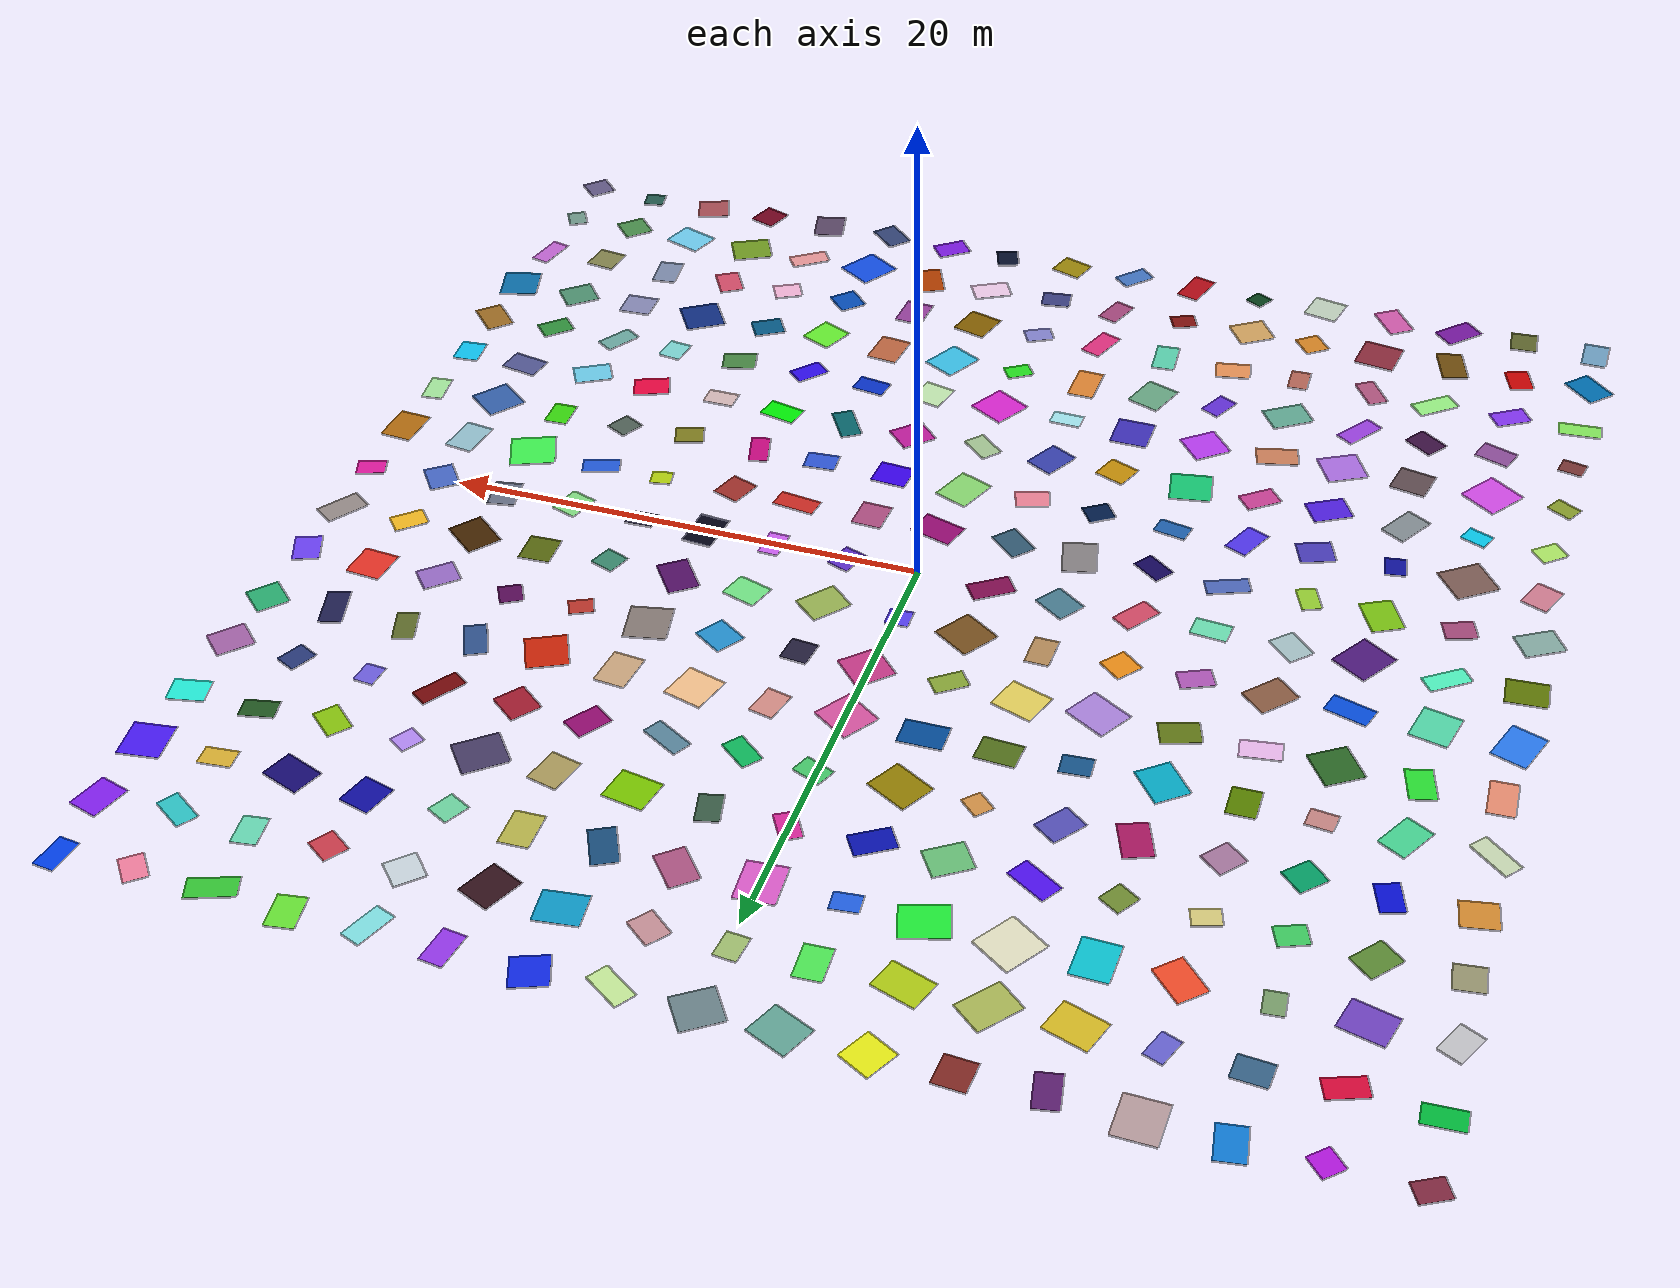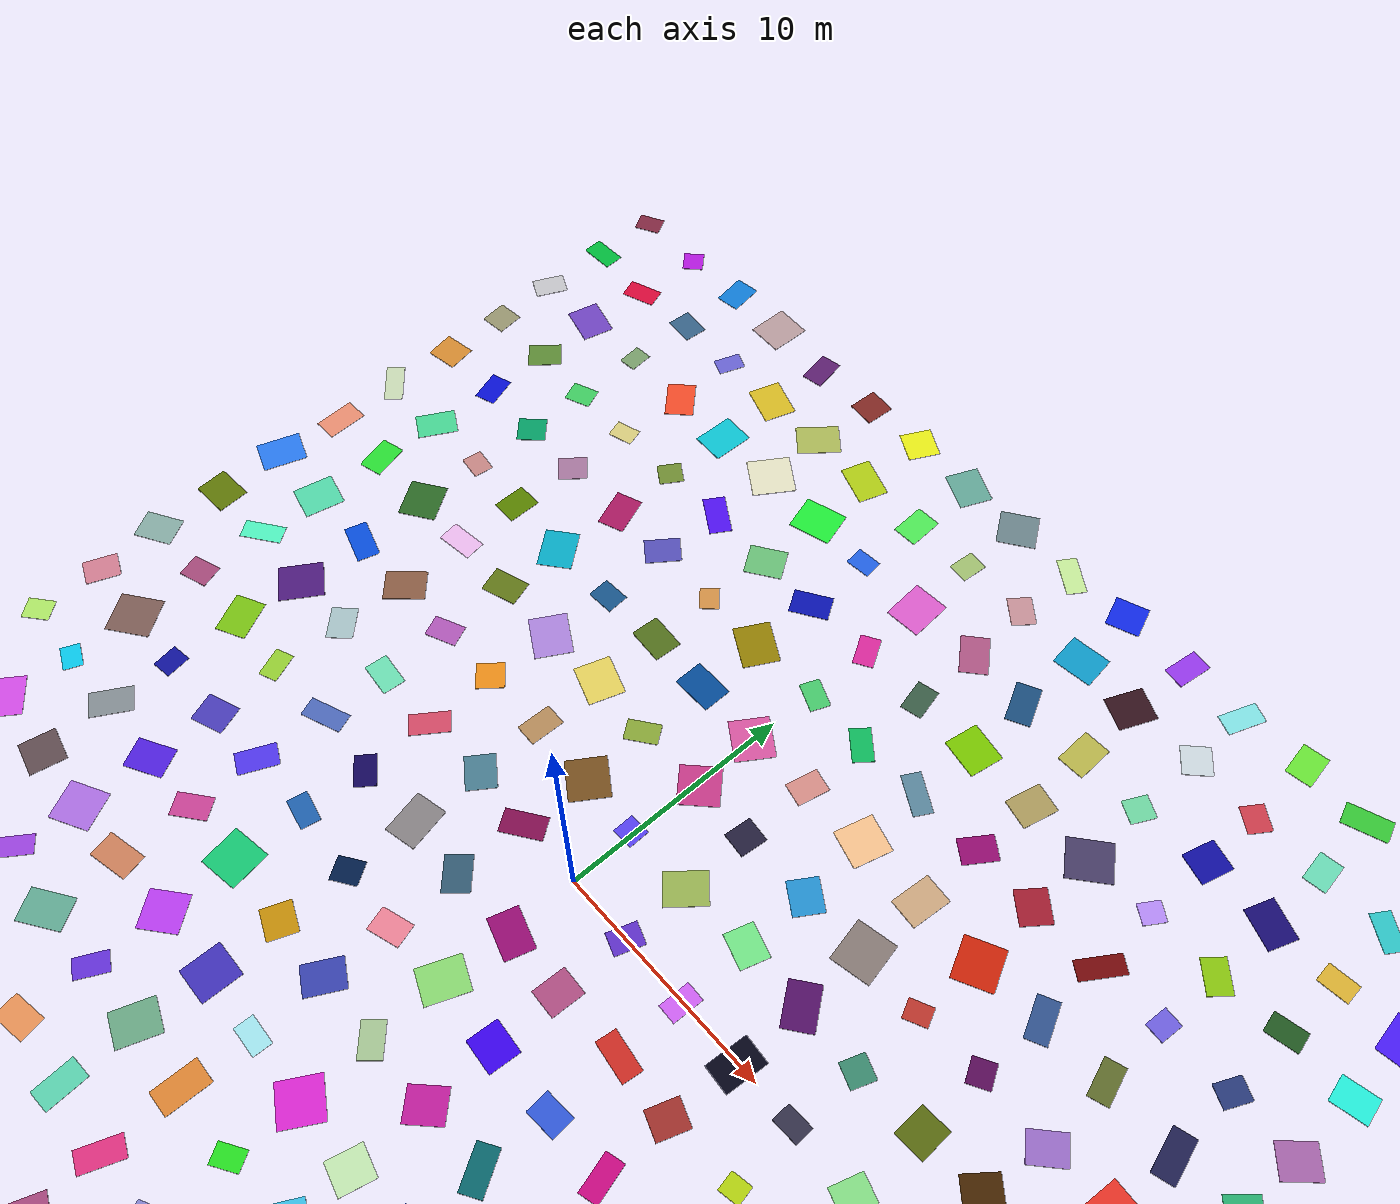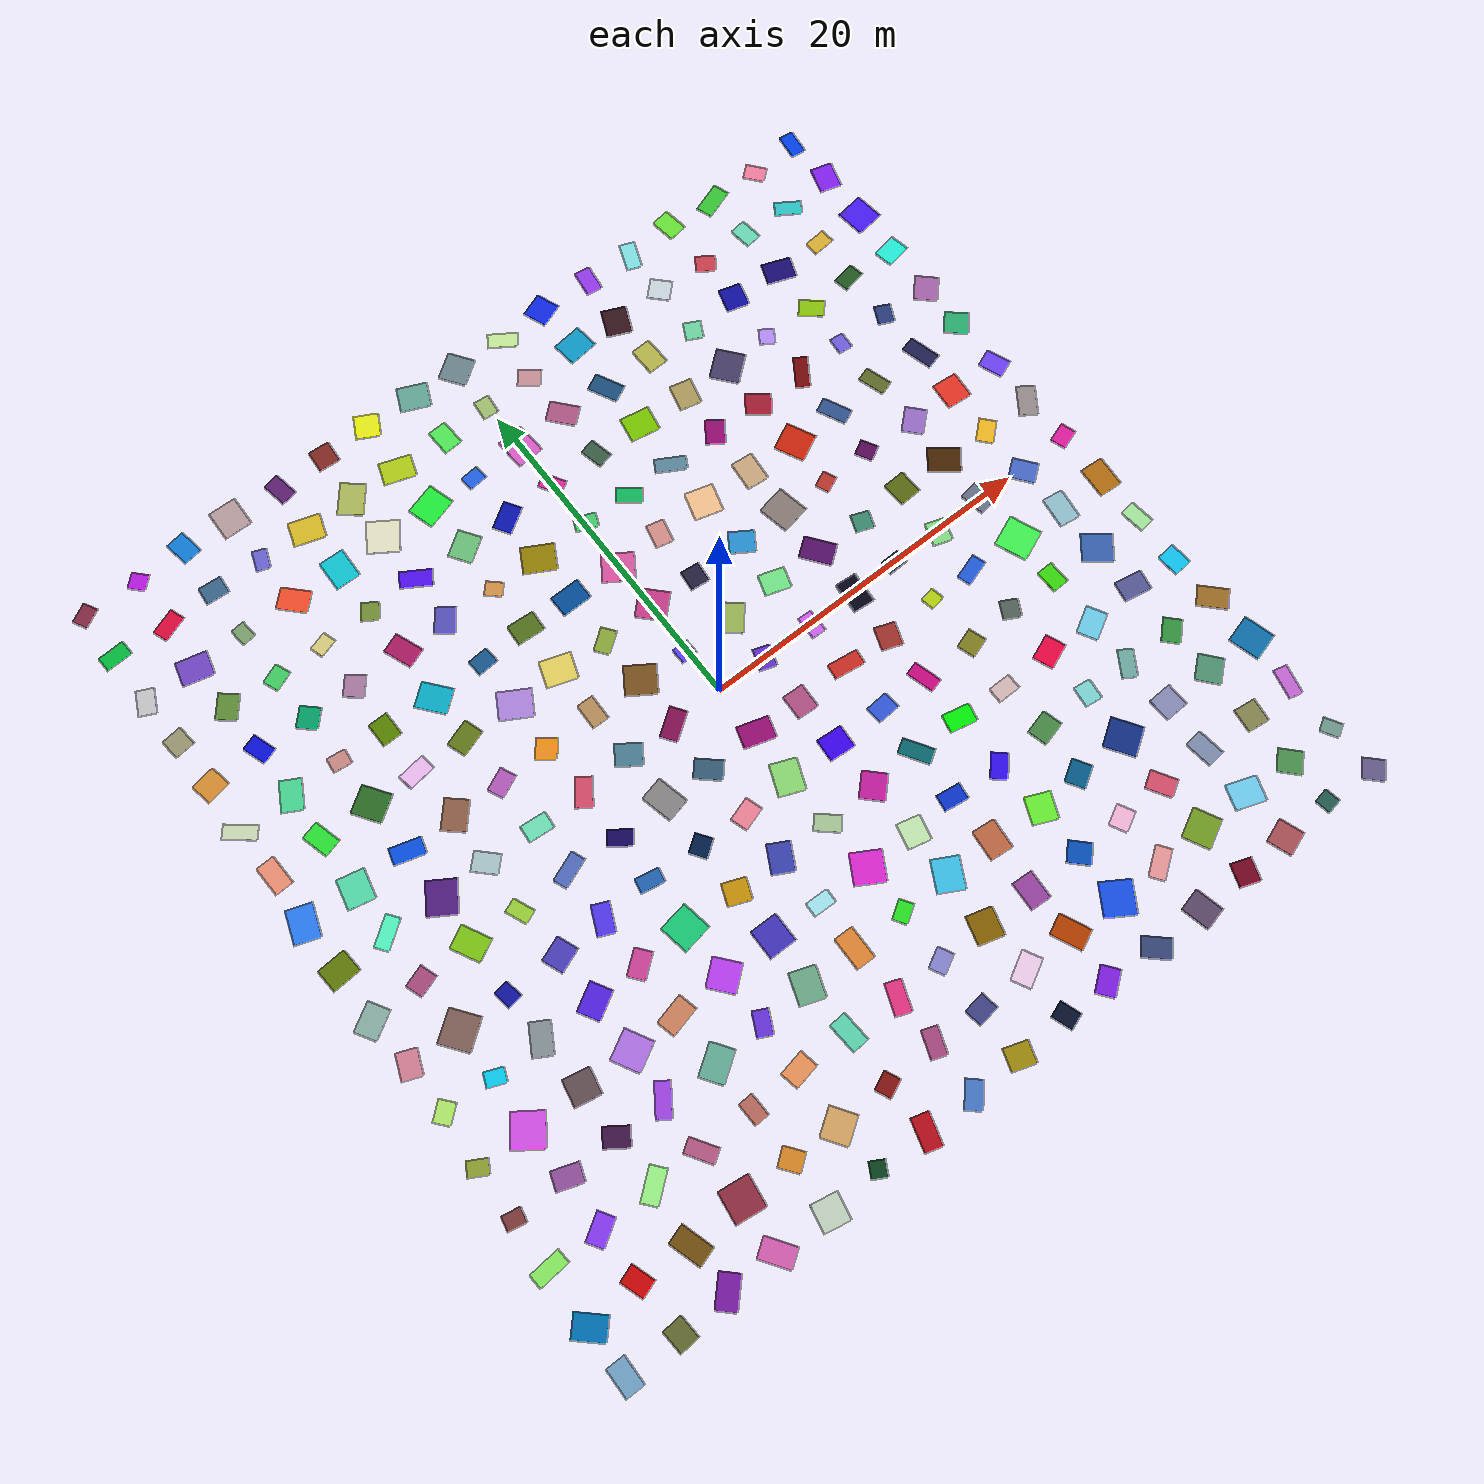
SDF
<sdf version="1.9">
 <world name="iris_runway">
  <physics name="1ms" type="ignore">
   <max_step_size>0.001</max_step_size>
   <real_time_factor>1.0</real_time_factor>
  </physics>
  <plugin filename="gz-sim-physics-system" name="gz::sim::systems::Physics"/>
  <plugin filename="gz-sim-sensors-system" name="gz::sim::systems::Sensors">
   <render_engine>ogre2</render_engine>
  </plugin>
  <plugin filename="gz-sim-user-commands-system" name="gz::sim::systems::UserCommands"/>
  <plugin filename="gz-sim-scene-broadcaster-system" name="gz::sim::systems::SceneBroadcaster"/>
  <plugin filename="gz-sim-imu-system" name="gz::sim::systems::Imu"/>
  <plugin filename="gz-sim-navsat-system" name="gz::sim::systems::NavSat"/>
  <scene><ambient>1.0 1.0 1.0</ambient><background>0.8 0.8 0.8</background></scene>
  <spherical_coordinates>
   <latitude_deg>-35.363262</latitude_deg>
   <longitude_deg>149.165237</longitude_deg>
   <elevation>584</elevation>
   <heading_deg>0</heading_deg>
   <surface_model>EARTH_WGS84</surface_model>
  </spherical_coordinates>
  <light type="directional" name="sun">
   <pose>0 0 10 0 0 0</pose>
   <diffuse>0.8 0.8 0.8 1</diffuse>
   <specular>0.8 0.8 0.8 1</specular>
   <attenuation>
    <range>1000</range>
    <constant>0.9</constant>
    <linear>0.01</linear>
    <quadratic>0.001</quadratic>
   </attenuation>
   <direction>-0.5 0.1 -0.9</direction>
  </light>
  <model name="axes">
   <static>1</static>
   <link name="link">
    <visual name="r">
     <cast_shadows>0</cast_shadows>
     <pose>5 0 0.1 0 0 0</pose>
     <geometry><box><size>10 0.01 0.01</size></box></geometry>
     <material>
      <ambient>1 0 0 0.8</ambient>
      <diffuse>1 0 0 0.8</diffuse>
      <emissive>1 0 0 0.8</emissive>
      <specular>0.5 0.5 0.5 0.8</specular>
     </material>
    </visual>
    <visual name="g">
     <cast_shadows>0</cast_shadows>
     <pose>0 5 0.1 0 0 0</pose>
     <geometry><box><size>0.01 10 0.01</size></box></geometry>
     <material>
      <ambient>0 1 0 0.8</ambient>
      <diffuse>0 1 0 0.8</diffuse>
      <emissive>0 1 0 0.8</emissive>
      <specular>0.5 0.5 0.5 0.8</specular>
     </material>
    </visual>
    <visual name="b">
     <cast_shadows>0</cast_shadows>
     <pose>0 0 5.1 0 0 0</pose>
     <geometry><box><size>0.01 0.01 10</size></box></geometry>
     <material>
      <ambient>0 0 1 0.8</ambient>
      <diffuse>0 0 1 0.8</diffuse>
      <emissive>0 0 1 0.8</emissive>
      <specular>0.5 0.5 0.5 0.8</specular>
     </material>
    </visual>
    <sensor name="navsat_sensor" type="navsat"><always_on>1</always_on><update_rate>1</update_rate></sensor>
   </link>
  </model>
  <model name="tiles">
   <static>true</static>
   <link name="l">
    <visual name="t0">
     <pose>-24.11 -23.90 0.01 0 0 1.56</pose>
     <geometry><box><size>1.64 1.08 0.02</size></box></geometry>
     <material><ambient>0.45 0.65 0.79 1</ambient><diffuse>0.45 0.65 0.79 1</diffuse></material>
    </visual>
    <visual name="t1">
     <pose>-24.12 -21.14 0.01 0 0 2.39</pose>
     <geometry><box><size>1.72 1.28 0.02</size></box></geometry>
     <material><ambient>0.00 0.45 0.72 1</ambient><diffuse>0.00 0.45 0.72 1</diffuse></material>
    </visual>
    <visual name="t2">
     <pose>-24.08 -17.87 0.01 0 0 0.08</pose>
     <geometry><box><size>1.79 0.83 0.02</size></box></geometry>
     <material><ambient>0.54 0.94 0.38 1</ambient><diffuse>0.54 0.94 0.38 1</diffuse></material>
    </visual>
    <visual name="t3">
     <pose>-24.09 -15.02 0.01 0 0 1.37</pose>
     <geometry><box><size>0.83 1.04 0.02</size></box></geometry>
     <material><ambient>0.50 0.23 0.23 1</ambient><diffuse>0.50 0.23 0.23 1</diffuse></material>
    </visual>
    <visual name="t4">
     <pose>-24.08 -12.01 0.01 0 0 2.63</pose>
     <geometry><box><size>1.12 0.82 0.02</size></box></geometry>
     <material><ambient>0.56 0.64 0.19 1</ambient><diffuse>0.56 0.64 0.19 1</diffuse></material>
    </visual>
    <visual name="t5">
     <pose>-23.85 -8.89 0.01 0 0 2.27</pose>
     <geometry><box><size>0.93 1.17 0.02</size></box></geometry>
     <material><ambient>0.71 0.94 0.42 1</ambient><diffuse>0.71 0.94 0.42 1</diffuse></material>
    </visual>
    <visual name="t6">
     <pose>-23.90 -5.95 0.01 0 0 2.77</pose>
     <geometry><box><size>1.13 1.45 0.02</size></box></geometry>
     <material><ambient>0.85 0.51 0.59 1</ambient><diffuse>0.85 0.51 0.59 1</diffuse></material>
    </visual>
    <visual name="t7">
     <pose>-24.14 -3.08 0.01 0 0 0.54</pose>
     <geometry><box><size>1.68 1.26 0.02</size></box></geometry>
     <material><ambient>0.55 0.70 0.67 1</ambient><diffuse>0.55 0.70 0.67 1</diffuse></material>
    </visual>
    <visual name="t8">
     <pose>-24.04 -0.02 0.01 0 0 1.64</pose>
     <geometry><box><size>1.36 1.66 0.02</size></box></geometry>
     <material><ambient>0.39 0.49 0.03 1</ambient><diffuse>0.39 0.49 0.03 1</diffuse></material>
    </visual>
    <visual name="t9">
     <pose>-24.14 3.06 0.01 0 0 1.24</pose>
     <geometry><box><size>1.88 1.45 0.02</size></box></geometry>
     <material><ambient>0.17 0.50 0.98 1</ambient><diffuse>0.17 0.50 0.98 1</diffuse></material>
    </visual>
    <visual name="t10">
     <pose>-23.92 6.01 0.01 0 0 1.61</pose>
     <geometry><box><size>1.75 1.06 0.02</size></box></geometry>
     <material><ambient>0.95 0.58 0.46 1</ambient><diffuse>0.95 0.58 0.46 1</diffuse></material>
    </visual>
    <visual name="t11">
     <pose>-24.07 9.01 0.01 0 0 2.46</pose>
     <geometry><box><size>1.85 0.81 0.02</size></box></geometry>
     <material><ambient>0.82 0.89 0.74 1</ambient><diffuse>0.82 0.89 0.74 1</diffuse></material>
    </visual>
    <visual name="t12">
     <pose>-23.91 12.01 0.01 0 0 0.18</pose>
     <geometry><box><size>1.42 1.27 0.02</size></box></geometry>
     <material><ambient>0.87 0.57 0.20 1</ambient><diffuse>0.87 0.57 0.20 1</diffuse></material>
    </visual>
    <visual name="t13">
     <pose>-24.00 15.00 0.01 0 0 1.69</pose>
     <geometry><box><size>1.19 1.18 0.02</size></box></geometry>
     <material><ambient>0.62 0.61 0.46 1</ambient><diffuse>0.62 0.61 0.46 1</diffuse></material>
    </visual>
    <visual name="t14">
     <pose>-24.14 17.92 0.01 0 0 2.70</pose>
     <geometry><box><size>0.99 1.44 0.02</size></box></geometry>
     <material><ambient>0.80 0.80 0.82 1</ambient><diffuse>0.80 0.80 0.82 1</diffuse></material>
    </visual>
    <visual name="t15">
     <pose>-24.07 21.10 0.01 0 0 0.05</pose>
     <geometry><box><size>1.54 0.89 0.02</size></box></geometry>
     <material><ambient>0.01 0.76 0.25 1</ambient><diffuse>0.01 0.76 0.25 1</diffuse></material>
    </visual>
    <visual name="t16">
     <pose>-24.12 24.04 0.01 0 0 0.50</pose>
     <geometry><box><size>1.18 0.88 0.02</size></box></geometry>
     <material><ambient>0.53 0.17 0.27 1</ambient><diffuse>0.53 0.17 0.27 1</diffuse></material>
    </visual>
    <visual name="t17">
     <pose>-20.94 -24.01 0.01 0 0 0.07</pose>
     <geometry><box><size>1.15 1.32 0.02</size></box></geometry>
     <material><ambient>0.39 0.42 0.19 1</ambient><diffuse>0.39 0.42 0.19 1</diffuse></material>
    </visual>
    <visual name="t18">
     <pose>-21.12 -20.88 0.01 0 0 1.90</pose>
     <geometry><box><size>1.36 1.03 0.02</size></box></geometry>
     <material><ambient>0.82 0.02 0.02 1</ambient><diffuse>0.82 0.02 0.02 1</diffuse></material>
    </visual>
    <visual name="t19">
     <pose>-21.11 -17.93 0.01 0 0 2.13</pose>
     <geometry><box><size>0.98 1.58 0.02</size></box></geometry>
     <material><ambient>0.54 0.22 0.98 1</ambient><diffuse>0.54 0.22 0.98 1</diffuse></material>
    </visual>
    <visual name="t20">
     <pose>-20.91 -15.00 0.01 0 0 1.24</pose>
     <geometry><box><size>1.05 1.51 0.02</size></box></geometry>
     <material><ambient>0.58 0.32 0.63 1</ambient><diffuse>0.58 0.32 0.63 1</diffuse></material>
    </visual>
    <visual name="t21">
     <pose>-21.13 -12.06 0.01 0 0 0.96</pose>
     <geometry><box><size>1.86 1.76 0.02</size></box></geometry>
     <material><ambient>0.86 0.31 0.94 1</ambient><diffuse>0.86 0.31 0.94 1</diffuse></material>
    </visual>
    <visual name="t22">
     <pose>-20.93 -9.03 0.01 0 0 2.76</pose>
     <geometry><box><size>1.08 0.81 0.02</size></box></geometry>
     <material><ambient>0.04 0.82 0.96 1</ambient><diffuse>0.04 0.82 0.96 1</diffuse></material>
    </visual>
    <visual name="t23">
     <pose>-20.98 -6.10 0.01 0 0 2.21</pose>
     <geometry><box><size>1.75 1.87 0.02</size></box></geometry>
     <material><ambient>0.51 0.38 0.35 1</ambient><diffuse>0.51 0.38 0.35 1</diffuse></material>
    </visual>
    <visual name="t24">
     <pose>-21.09 -2.95 0.01 0 0 0.33</pose>
     <geometry><box><size>1.28 1.01 0.02</size></box></geometry>
     <material><ambient>0.67 0.30 0.50 1</ambient><diffuse>0.67 0.30 0.50 1</diffuse></material>
    </visual>
    <visual name="t25">
     <pose>-21.05 0.11 0.01 0 0 0.63</pose>
     <geometry><box><size>1.79 0.82 0.02</size></box></geometry>
     <material><ambient>0.33 0.99 0.78 1</ambient><diffuse>0.33 0.99 0.78 1</diffuse></material>
    </visual>
    <visual name="t26">
     <pose>-21.05 2.91 0.01 0 0 2.93</pose>
     <geometry><box><size>1.54 1.72 0.02</size></box></geometry>
     <material><ambient>0.34 0.88 0.69 1</ambient><diffuse>0.34 0.88 0.69 1</diffuse></material>
    </visual>
    <visual name="t27">
     <pose>-21.00 6.15 0.01 0 0 0.27</pose>
     <geometry><box><size>1.06 1.60 0.02</size></box></geometry>
     <material><ambient>0.17 0.91 0.21 1</ambient><diffuse>0.17 0.91 0.21 1</diffuse></material>
    </visual>
    <visual name="t28">
     <pose>-20.92 9.03 0.01 0 0 1.07</pose>
     <geometry><box><size>1.73 1.20 0.02</size></box></geometry>
     <material><ambient>0.29 0.87 0.60 1</ambient><diffuse>0.29 0.87 0.60 1</diffuse></material>
    </visual>
    <visual name="t29">
     <pose>-20.86 12.12 0.01 0 0 0.33</pose>
     <geometry><box><size>0.95 1.41 0.02</size></box></geometry>
     <material><ambient>0.04 0.07 0.87 1</ambient><diffuse>0.04 0.07 0.87 1</diffuse></material>
    </visual>
    <visual name="t30">
     <pose>-20.91 15.10 0.01 0 0 2.46</pose>
     <geometry><box><size>1.17 1.48 0.02</size></box></geometry>
     <material><ambient>0.38 0.57 0.22 1</ambient><diffuse>0.38 0.57 0.22 1</diffuse></material>
    </visual>
    <visual name="t31">
     <pose>-21.13 17.93 0.01 0 0 2.90</pose>
     <geometry><box><size>1.78 1.42 0.02</size></box></geometry>
     <material><ambient>0.46 0.28 0.79 1</ambient><diffuse>0.46 0.28 0.79 1</diffuse></material>
    </visual>
    <visual name="t32">
     <pose>-20.90 20.85 0.01 0 0 0.36</pose>
     <geometry><box><size>1.54 0.90 0.02</size></box></geometry>
     <material><ambient>0.89 0.04 0.24 1</ambient><diffuse>0.89 0.04 0.24 1</diffuse></material>
    </visual>
    <visual name="t33">
     <pose>-20.85 23.98 0.01 0 0 0.76</pose>
     <geometry><box><size>0.93 0.98 0.02</size></box></geometry>
     <material><ambient>0.74 0.10 0.91 1</ambient><diffuse>0.74 0.10 0.91 1</diffuse></material>
    </visual>
    <visual name="t34">
     <pose>-18.04 -23.86 0.01 0 0 0.80</pose>
     <geometry><box><size>1.80 1.12 0.02</size></box></geometry>
     <material><ambient>0.48 0.10 0.65 1</ambient><diffuse>0.48 0.10 0.65 1</diffuse></material>
    </visual>
    <visual name="t35">
     <pose>-18.14 -21.15 0.01 0 0 1.87</pose>
     <geometry><box><size>1.88 1.13 0.02</size></box></geometry>
     <material><ambient>0.45 0.31 0.06 1</ambient><diffuse>0.45 0.31 0.06 1</diffuse></material>
    </visual>
    <visual name="t36">
     <pose>-17.88 -17.86 0.01 0 0 0.68</pose>
     <geometry><box><size>1.87 0.92 0.02</size></box></geometry>
     <material><ambient>0.62 0.98 0.54 1</ambient><diffuse>0.62 0.98 0.54 1</diffuse></material>
    </visual>
    <visual name="t37">
     <pose>-17.94 -14.95 0.01 0 0 0.96</pose>
     <geometry><box><size>1.08 1.40 0.02</size></box></geometry>
     <material><ambient>0.25 0.08 0.28 1</ambient><diffuse>0.25 0.08 0.28 1</diffuse></material>
    </visual>
    <visual name="t38">
     <pose>-17.85 -12.02 0.01 0 0 2.95</pose>
     <geometry><box><size>1.52 1.51 0.02</size></box></geometry>
     <material><ambient>0.39 0.31 0.33 1</ambient><diffuse>0.39 0.31 0.33 1</diffuse></material>
    </visual>
    <visual name="t39">
     <pose>-18.05 -8.90 0.01 0 0 1.05</pose>
     <geometry><box><size>1.78 1.13 0.02</size></box></geometry>
     <material><ambient>0.54 0.58 0.60 1</ambient><diffuse>0.54 0.58 0.60 1</diffuse></material>
    </visual>
    <visual name="t40">
     <pose>-18.08 -6.14 0.01 0 0 1.73</pose>
     <geometry><box><size>1.07 0.88 0.02</size></box></geometry>
     <material><ambient>0.07 0.08 0.64 1</ambient><diffuse>0.07 0.08 0.64 1</diffuse></material>
    </visual>
    <visual name="t41">
     <pose>-18.06 -2.91 0.01 0 0 0.48</pose>
     <geometry><box><size>1.34 1.75 0.02</size></box></geometry>
     <material><ambient>0.50 0.79 0.08 1</ambient><diffuse>0.50 0.79 0.08 1</diffuse></material>
    </visual>
    <visual name="t42">
     <pose>-17.87 -0.10 0.01 0 0 2.58</pose>
     <geometry><box><size>1.65 1.88 0.02</size></box></geometry>
     <material><ambient>0.32 0.11 0.51 1</ambient><diffuse>0.32 0.11 0.51 1</diffuse></material>
    </visual>
    <visual name="t43">
     <pose>-17.87 2.94 0.01 0 0 2.86</pose>
     <geometry><box><size>1.78 0.96 0.02</size></box></geometry>
     <material><ambient>0.03 0.32 0.90 1</ambient><diffuse>0.03 0.32 0.90 1</diffuse></material>
    </visual>
    <visual name="t44">
     <pose>-17.91 6.12 0.01 0 0 2.17</pose>
     <geometry><box><size>1.72 1.62 0.02</size></box></geometry>
     <material><ambient>0.18 0.43 0.16 1</ambient><diffuse>0.18 0.43 0.16 1</diffuse></material>
    </visual>
    <visual name="t45">
     <pose>-17.94 9.05 0.01 0 0 3.03</pose>
     <geometry><box><size>1.08 0.87 0.02</size></box></geometry>
     <material><ambient>0.81 0.55 0.54 1</ambient><diffuse>0.81 0.55 0.54 1</diffuse></material>
    </visual>
    <visual name="t46">
     <pose>-17.89 11.99 0.01 0 0 0.81</pose>
     <geometry><box><size>1.24 1.17 0.02</size></box></geometry>
     <material><ambient>0.02 0.65 0.42 1</ambient><diffuse>0.02 0.65 0.42 1</diffuse></material>
    </visual>
    <visual name="t47">
     <pose>-17.98 14.87 0.01 0 0 0.39</pose>
     <geometry><box><size>1.19 0.95 0.02</size></box></geometry>
     <material><ambient>0.26 0.83 0.40 1</ambient><diffuse>0.26 0.83 0.40 1</diffuse></material>
    </visual>
    <visual name="t48">
     <pose>-18.03 18.03 0.01 0 0 1.66</pose>
     <geometry><box><size>1.06 0.81 0.02</size></box></geometry>
     <material><ambient>0.50 0.65 0.44 1</ambient><diffuse>0.50 0.65 0.44 1</diffuse></material>
    </visual>
    <visual name="t49">
     <pose>-17.94 21.07 0.01 0 0 1.50</pose>
     <geometry><box><size>1.06 1.34 0.02</size></box></geometry>
     <material><ambient>0.23 0.41 0.56 1</ambient><diffuse>0.23 0.41 0.56 1</diffuse></material>
    </visual>
    <visual name="t50">
     <pose>-17.88 24.13 0.01 0 0 0.15</pose>
     <geometry><box><size>1.10 1.51 0.02</size></box></geometry>
     <material><ambient>0.07 0.51 0.88 1</ambient><diffuse>0.07 0.51 0.88 1</diffuse></material>
    </visual>
    <visual name="t51">
     <pose>-15.10 -23.92 0.01 0 0 2.17</pose>
     <geometry><box><size>1.77 1.14 0.02</size></box></geometry>
     <material><ambient>0.85 0.37 0.70 1</ambient><diffuse>0.85 0.37 0.70 1</diffuse></material>
    </visual>
    <visual name="t52">
     <pose>-14.93 -20.97 0.01 0 0 3.01</pose>
     <geometry><box><size>1.74 1.79 0.02</size></box></geometry>
     <material><ambient>0.57 0.18 0.25 1</ambient><diffuse>0.57 0.18 0.25 1</diffuse></material>
    </visual>
    <visual name="t53">
     <pose>-15.08 -17.98 0.01 0 0 2.14</pose>
     <geometry><box><size>1.63 0.86 0.02</size></box></geometry>
     <material><ambient>0.72 0.35 0.52 1</ambient><diffuse>0.72 0.35 0.52 1</diffuse></material>
    </visual>
    <visual name="t54">
     <pose>-15.10 -14.93 0.01 0 0 2.54</pose>
     <geometry><box><size>0.84 1.88 0.02</size></box></geometry>
     <material><ambient>0.63 0.27 0.91 1</ambient><diffuse>0.63 0.27 0.91 1</diffuse></material>
    </visual>
    <visual name="t55">
     <pose>-14.86 -12.11 0.01 0 0 2.07</pose>
     <geometry><box><size>1.65 1.73 0.02</size></box></geometry>
     <material><ambient>0.70 0.45 0.92 1</ambient><diffuse>0.70 0.45 0.92 1</diffuse></material>
    </visual>
    <visual name="t56">
     <pose>-14.86 -9.04 0.01 0 0 0.52</pose>
     <geometry><box><size>1.68 1.28 0.02</size></box></geometry>
     <material><ambient>0.33 0.13 0.91 1</ambient><diffuse>0.33 0.13 0.91 1</diffuse></material>
    </visual>
    <visual name="t57">
     <pose>-14.86 -6.11 0.01 0 0 0.37</pose>
     <geometry><box><size>1.46 1.25 0.02</size></box></geometry>
     <material><ambient>0.30 0.25 0.75 1</ambient><diffuse>0.30 0.25 0.75 1</diffuse></material>
    </visual>
    <visual name="t58">
     <pose>-15.15 -3.09 0.01 0 0 1.97</pose>
     <geometry><box><size>1.28 0.82 0.02</size></box></geometry>
     <material><ambient>0.61 0.84 0.21 1</ambient><diffuse>0.61 0.84 0.21 1</diffuse></material>
    </visual>
    <visual name="t59">
     <pose>-15.06 0.01 0.01 0 0 0.79</pose>
     <geometry><box><size>1.10 1.44 0.02</size></box></geometry>
     <material><ambient>0.68 0.79 0.81 1</ambient><diffuse>0.68 0.79 0.81 1</diffuse></material>
    </visual>
    <visual name="t60">
     <pose>-14.86 3.01 0.01 0 0 2.41</pose>
     <geometry><box><size>1.34 1.74 0.02</size></box></geometry>
     <material><ambient>0.57 0.38 0.28 1</ambient><diffuse>0.57 0.38 0.28 1</diffuse></material>
    </visual>
    <visual name="t61">
     <pose>-15.12 6.09 0.01 0 0 1.71</pose>
     <geometry><box><size>0.93 1.62 0.02</size></box></geometry>
     <material><ambient>0.96 0.76 0.97 1</ambient><diffuse>0.96 0.76 0.97 1</diffuse></material>
    </visual>
    <visual name="t62">
     <pose>-15.11 9.00 0.01 0 0 1.58</pose>
     <geometry><box><size>1.43 1.14 0.02</size></box></geometry>
     <material><ambient>0.36 0.53 0.00 1</ambient><diffuse>0.36 0.53 0.00 1</diffuse></material>
    </visual>
    <visual name="t63">
     <pose>-15.02 11.98 0.01 0 0 2.46</pose>
     <geometry><box><size>1.14 1.24 0.02</size></box></geometry>
     <material><ambient>0.68 0.49 0.65 1</ambient><diffuse>0.68 0.49 0.65 1</diffuse></material>
    </visual>
    <visual name="t64">
     <pose>-15.04 14.91 0.01 0 0 1.88</pose>
     <geometry><box><size>0.80 1.11 0.02</size></box></geometry>
     <material><ambient>0.88 0.83 0.51 1</ambient><diffuse>0.88 0.83 0.51 1</diffuse></material>
    </visual>
    <visual name="t65">
     <pose>-14.85 17.99 0.01 0 0 2.34</pose>
     <geometry><box><size>1.72 1.25 0.02</size></box></geometry>
     <material><ambient>0.99 0.31 0.17 1</ambient><diffuse>0.99 0.31 0.17 1</diffuse></material>
    </visual>
    <visual name="t66">
     <pose>-14.96 21.01 0.01 0 0 1.22</pose>
     <geometry><box><size>1.20 0.80 0.02</size></box></geometry>
     <material><ambient>0.43 0.41 0.86 1</ambient><diffuse>0.43 0.41 0.86 1</diffuse></material>
    </visual>
    <visual name="t67">
     <pose>-14.97 24.07 0.01 0 0 1.55</pose>
     <geometry><box><size>1.79 1.62 0.02</size></box></geometry>
     <material><ambient>0.75 0.64 0.65 1</ambient><diffuse>0.75 0.64 0.65 1</diffuse></material>
    </visual>
    <visual name="t68">
     <pose>-11.96 -24.03 0.01 0 0 2.94</pose>
     <geometry><box><size>1.49 1.50 0.02</size></box></geometry>
     <material><ambient>0.78 0.85 0.77 1</ambient><diffuse>0.78 0.85 0.77 1</diffuse></material>
    </visual>
    <visual name="t69">
     <pose>-11.91 -20.97 0.01 0 0 2.22</pose>
     <geometry><box><size>1.18 1.09 0.02</size></box></geometry>
     <material><ambient>0.87 0.54 0.15 1</ambient><diffuse>0.87 0.54 0.15 1</diffuse></material>
    </visual>
    <visual name="t70">
     <pose>-11.90 -18.00 0.01 0 0 1.60</pose>
     <geometry><box><size>1.31 0.85 0.02</size></box></geometry>
     <material><ambient>0.74 0.42 0.36 1</ambient><diffuse>0.74 0.42 0.36 1</diffuse></material>
    </visual>
    <visual name="t71">
     <pose>-11.95 -15.14 0.01 0 0 2.17</pose>
     <geometry><box><size>1.36 1.84 0.02</size></box></geometry>
     <material><ambient>0.40 0.69 0.60 1</ambient><diffuse>0.40 0.69 0.60 1</diffuse></material>
    </visual>
    <visual name="t72">
     <pose>-12.09 -12.09 0.01 0 0 0.24</pose>
     <geometry><box><size>1.77 1.10 0.02</size></box></geometry>
     <material><ambient>0.83 0.52 0.37 1</ambient><diffuse>0.83 0.52 0.37 1</diffuse></material>
    </visual>
    <visual name="t73">
     <pose>-12.00 -8.93 0.01 0 0 2.24</pose>
     <geometry><box><size>0.99 1.52 0.02</size></box></geometry>
     <material><ambient>0.82 0.27 0.61 1</ambient><diffuse>0.82 0.27 0.61 1</diffuse></material>
    </visual>
    <visual name="t74">
     <pose>-12.08 -5.98 0.01 0 0 2.72</pose>
     <geometry><box><size>0.99 1.67 0.02</size></box></geometry>
     <material><ambient>0.33 0.22 0.96 1</ambient><diffuse>0.33 0.22 0.96 1</diffuse></material>
    </visual>
    <visual name="t75">
     <pose>-11.94 -2.90 0.01 0 0 1.95</pose>
     <geometry><box><size>0.83 1.79 0.02</size></box></geometry>
     <material><ambient>0.32 0.43 0.76 1</ambient><diffuse>0.32 0.43 0.76 1</diffuse></material>
    </visual>
    <visual name="t76">
     <pose>-11.91 -0.09 0.01 0 0 3.06</pose>
     <geometry><box><size>1.49 0.98 0.02</size></box></geometry>
     <material><ambient>0.44 0.91 0.73 1</ambient><diffuse>0.44 0.91 0.73 1</diffuse></material>
    </visual>
    <visual name="t77">
     <pose>-11.97 2.93 0.01 0 0 0.43</pose>
     <geometry><box><size>1.38 0.95 0.02</size></box></geometry>
     <material><ambient>0.72 0.36 0.75 1</ambient><diffuse>0.72 0.36 0.75 1</diffuse></material>
    </visual>
    <visual name="t78">
     <pose>-12.08 6.07 0.01 0 0 0.33</pose>
     <geometry><box><size>1.59 1.14 0.02</size></box></geometry>
     <material><ambient>0.40 0.49 0.10 1</ambient><diffuse>0.40 0.49 0.10 1</diffuse></material>
    </visual>
    <visual name="t79">
     <pose>-12.09 8.87 0.01 0 0 0.68</pose>
     <geometry><box><size>1.46 1.78 0.02</size></box></geometry>
     <material><ambient>0.03 0.70 0.81 1</ambient><diffuse>0.03 0.70 0.81 1</diffuse></material>
    </visual>
    <visual name="t80">
     <pose>-11.86 12.03 0.01 0 0 0.37</pose>
     <geometry><box><size>1.18 1.72 0.02</size></box></geometry>
     <material><ambient>0.69 0.10 0.40 1</ambient><diffuse>0.69 0.10 0.40 1</diffuse></material>
    </visual>
    <visual name="t81">
     <pose>-12.00 14.96 0.01 0 0 2.58</pose>
     <geometry><box><size>0.99 1.05 0.02</size></box></geometry>
     <material><ambient>0.46 0.58 0.21 1</ambient><diffuse>0.46 0.58 0.21 1</diffuse></material>
    </visual>
    <visual name="t82">
     <pose>-11.94 17.95 0.01 0 0 3.12</pose>
     <geometry><box><size>1.45 1.80 0.02</size></box></geometry>
     <material><ambient>0.05 0.80 0.86 1</ambient><diffuse>0.05 0.80 0.86 1</diffuse></material>
    </visual>
    <visual name="t83">
     <pose>-12.05 20.96 0.01 0 0 1.26</pose>
     <geometry><box><size>1.44 1.81 0.02</size></box></geometry>
     <material><ambient>0.88 0.76 0.15 1</ambient><diffuse>0.88 0.76 0.15 1</diffuse></material>
    </visual>
    <visual name="t84">
     <pose>-11.88 23.85 0.01 0 0 0.18</pose>
     <geometry><box><size>0.96 1.53 0.02</size></box></geometry>
     <material><ambient>0.38 0.13 0.46 1</ambient><diffuse>0.38 0.13 0.46 1</diffuse></material>
    </visual>
    <visual name="t85">
     <pose>-8.90 -23.88 0.01 0 0 2.64</pose>
     <geometry><box><size>0.84 0.87 0.02</size></box></geometry>
     <material><ambient>0.04 0.27 0.12 1</ambient><diffuse>0.04 0.27 0.12 1</diffuse></material>
    </visual>
    <visual name="t86">
     <pose>-9.12 -21.14 0.01 0 0 2.16</pose>
     <geometry><box><size>1.50 1.62 0.02</size></box></geometry>
     <material><ambient>0.85 0.66 0.39 1</ambient><diffuse>0.85 0.66 0.39 1</diffuse></material>
    </visual>
    <visual name="t87">
     <pose>-8.96 -17.86 0.01 0 0 0.19</pose>
     <geometry><box><size>1.51 1.07 0.02</size></box></geometry>
     <material><ambient>0.94 0.59 0.35 1</ambient><diffuse>0.94 0.59 0.35 1</diffuse></material>
    </visual>
    <visual name="t88">
     <pose>-8.97 -14.98 0.01 0 0 1.11</pose>
     <geometry><box><size>1.37 0.87 0.02</size></box></geometry>
     <material><ambient>0.41 0.20 0.88 1</ambient><diffuse>0.41 0.20 0.88 1</diffuse></material>
    </visual>
    <visual name="t89">
     <pose>-9.02 -11.95 0.01 0 0 2.26</pose>
     <geometry><box><size>1.58 1.62 0.02</size></box></geometry>
     <material><ambient>0.75 0.25 0.98 1</ambient><diffuse>0.75 0.25 0.98 1</diffuse></material>
    </visual>
    <visual name="t90">
     <pose>-9.10 -8.87 0.01 0 0 0.17</pose>
     <geometry><box><size>1.74 1.74 0.02</size></box></geometry>
     <material><ambient>0.09 0.81 0.47 1</ambient><diffuse>0.09 0.81 0.47 1</diffuse></material>
    </visual>
    <visual name="t91">
     <pose>-9.04 -5.85 0.01 0 0 1.39</pose>
     <geometry><box><size>0.84 1.38 0.02</size></box></geometry>
     <material><ambient>0.13 0.40 0.71 1</ambient><diffuse>0.13 0.40 0.71 1</diffuse></material>
    </visual>
    <visual name="t92">
     <pose>-8.89 -3.14 0.01 0 0 2.51</pose>
     <geometry><box><size>1.38 0.90 0.02</size></box></geometry>
     <material><ambient>0.09 0.03 0.38 1</ambient><diffuse>0.09 0.03 0.38 1</diffuse></material>
    </visual>
    <visual name="t93">
     <pose>-8.93 -0.06 0.01 0 0 2.53</pose>
     <geometry><box><size>0.94 1.67 0.02</size></box></geometry>
     <material><ambient>0.86 0.30 0.42 1</ambient><diffuse>0.86 0.30 0.42 1</diffuse></material>
    </visual>
    <visual name="t94">
     <pose>-9.08 3.02 0.01 0 0 2.46</pose>
     <geometry><box><size>1.16 1.17 0.02</size></box></geometry>
     <material><ambient>0.96 0.58 0.10 1</ambient><diffuse>0.96 0.58 0.10 1</diffuse></material>
    </visual>
    <visual name="t95">
     <pose>-8.95 5.98 0.01 0 0 2.62</pose>
     <geometry><box><size>1.89 1.59 0.02</size></box></geometry>
     <material><ambient>0.70 0.54 0.90 1</ambient><diffuse>0.70 0.54 0.90 1</diffuse></material>
    </visual>
    <visual name="t96">
     <pose>-8.90 8.94 0.01 0 0 1.64</pose>
     <geometry><box><size>0.97 1.21 0.02</size></box></geometry>
     <material><ambient>0.10 0.35 0.57 1</ambient><diffuse>0.10 0.35 0.57 1</diffuse></material>
    </visual>
    <visual name="t97">
     <pose>-9.14 12.09 0.01 0 0 0.94</pose>
     <geometry><box><size>1.52 1.15 0.02</size></box></geometry>
     <material><ambient>0.35 0.33 0.75 1</ambient><diffuse>0.35 0.33 0.75 1</diffuse></material>
    </visual>
    <visual name="t98">
     <pose>-9.00 15.01 0.01 0 0 1.02</pose>
     <geometry><box><size>0.96 1.81 0.02</size></box></geometry>
     <material><ambient>0.33 0.07 0.98 1</ambient><diffuse>0.33 0.07 0.98 1</diffuse></material>
    </visual>
    <visual name="t99">
     <pose>-9.01 18.12 0.01 0 0 2.56</pose>
     <geometry><box><size>1.82 1.87 0.02</size></box></geometry>
     <material><ambient>0.93 0.92 0.80 1</ambient><diffuse>0.93 0.92 0.80 1</diffuse></material>
    </visual>
    <visual name="t100">
     <pose>-9.11 21.01 0.01 0 0 2.46</pose>
     <geometry><box><size>1.43 1.89 0.02</size></box></geometry>
     <material><ambient>0.70 0.75 0.36 1</ambient><diffuse>0.70 0.75 0.36 1</diffuse></material>
    </visual>
    <visual name="t101">
     <pose>-8.87 24.04 0.01 0 0 3.08</pose>
     <geometry><box><size>1.24 1.31 0.02</size></box></geometry>
     <material><ambient>0.53 0.17 0.15 1</ambient><diffuse>0.53 0.17 0.15 1</diffuse></material>
    </visual>
    <visual name="t102">
     <pose>-5.94 -23.98 0.01 0 0 1.29</pose>
     <geometry><box><size>1.80 1.00 0.02</size></box></geometry>
     <material><ambient>0.73 0.05 0.10 1</ambient><diffuse>0.73 0.05 0.10 1</diffuse></material>
    </visual>
    <visual name="t103">
     <pose>-5.99 -21.07 0.01 0 0 1.98</pose>
     <geometry><box><size>0.92 1.09 0.02</size></box></geometry>
     <material><ambient>0.53 0.08 0.07 1</ambient><diffuse>0.53 0.08 0.07 1</diffuse></material>
    </visual>
    <visual name="t104">
     <pose>-5.89 -17.96 0.01 0 0 0.07</pose>
     <geometry><box><size>0.99 1.75 0.02</size></box></geometry>
     <material><ambient>0.37 0.85 0.71 1</ambient><diffuse>0.37 0.85 0.71 1</diffuse></material>
    </visual>
    <visual name="t105">
     <pose>-6.06 -14.88 0.01 0 0 2.80</pose>
     <geometry><box><size>1.46 1.75 0.02</size></box></geometry>
     <material><ambient>0.43 0.68 0.54 1</ambient><diffuse>0.43 0.68 0.54 1</diffuse></material>
    </visual>
    <visual name="t106">
     <pose>-5.87 -11.91 0.01 0 0 3.13</pose>
     <geometry><box><size>1.60 1.70 0.02</size></box></geometry>
     <material><ambient>0.26 0.20 0.75 1</ambient><diffuse>0.26 0.20 0.75 1</diffuse></material>
    </visual>
    <visual name="t107">
     <pose>-5.92 -9.00 0.01 0 0 2.77</pose>
     <geometry><box><size>1.34 1.24 0.02</size></box></geometry>
     <material><ambient>0.80 0.58 0.04 1</ambient><diffuse>0.80 0.58 0.04 1</diffuse></material>
    </visual>
    <visual name="t108">
     <pose>-5.89 -6.01 0.01 0 0 2.17</pose>
     <geometry><box><size>1.01 1.13 0.02</size></box></geometry>
     <material><ambient>0.01 0.12 0.30 1</ambient><diffuse>0.01 0.12 0.30 1</diffuse></material>
    </visual>
    <visual name="t109">
     <pose>-5.88 -2.93 0.01 0 0 1.80</pose>
     <geometry><box><size>1.87 1.40 0.02</size></box></geometry>
     <material><ambient>0.55 0.53 0.54 1</ambient><diffuse>0.55 0.53 0.54 1</diffuse></material>
    </visual>
    <visual name="t110">
     <pose>-5.90 0.14 0.01 0 0 0.97</pose>
     <geometry><box><size>1.25 1.49 0.02</size></box></geometry>
     <material><ambient>0.30 0.51 0.59 1</ambient><diffuse>0.30 0.51 0.59 1</diffuse></material>
    </visual>
    <visual name="t111">
     <pose>-5.99 3.14 0.01 0 0 3.12</pose>
     <geometry><box><size>0.98 1.50 0.02</size></box></geometry>
     <material><ambient>0.74 0.57 0.37 1</ambient><diffuse>0.74 0.57 0.37 1</diffuse></material>
    </visual>
    <visual name="t112">
     <pose>-6.03 6.13 0.01 0 0 2.82</pose>
     <geometry><box><size>1.78 1.54 0.02</size></box></geometry>
     <material><ambient>0.93 0.85 0.38 1</ambient><diffuse>0.93 0.85 0.38 1</diffuse></material>
    </visual>
    <visual name="t113">
     <pose>-6.01 9.09 0.01 0 0 1.51</pose>
     <geometry><box><size>1.21 1.62 0.02</size></box></geometry>
     <material><ambient>0.34 0.46 0.12 1</ambient><diffuse>0.34 0.46 0.12 1</diffuse></material>
    </visual>
    <visual name="t114">
     <pose>-6.04 11.97 0.01 0 0 0.82</pose>
     <geometry><box><size>0.82 0.99 0.02</size></box></geometry>
     <material><ambient>0.86 0.59 0.29 1</ambient><diffuse>0.86 0.59 0.29 1</diffuse></material>
    </visual>
    <visual name="t115">
     <pose>-5.85 14.93 0.01 0 0 2.17</pose>
     <geometry><box><size>1.37 1.61 0.02</size></box></geometry>
     <material><ambient>0.43 0.78 0.49 1</ambient><diffuse>0.43 0.78 0.49 1</diffuse></material>
    </visual>
    <visual name="t116">
     <pose>-5.94 18.00 0.01 0 0 0.29</pose>
     <geometry><box><size>1.87 1.59 0.02</size></box></geometry>
     <material><ambient>0.13 0.97 0.23 1</ambient><diffuse>0.13 0.97 0.23 1</diffuse></material>
    </visual>
    <visual name="t117">
     <pose>-6.14 20.93 0.01 0 0 1.25</pose>
     <geometry><box><size>1.33 1.85 0.02</size></box></geometry>
     <material><ambient>0.72 0.83 0.09 1</ambient><diffuse>0.72 0.83 0.09 1</diffuse></material>
    </visual>
    <visual name="t118">
     <pose>-5.97 24.15 0.01 0 0 1.09</pose>
     <geometry><box><size>1.40 1.39 0.02</size></box></geometry>
     <material><ambient>0.95 0.97 0.10 1</ambient><diffuse>0.95 0.97 0.10 1</diffuse></material>
    </visual>
    <visual name="t119">
     <pose>-2.98 -24.02 0.01 0 0 0.83</pose>
     <geometry><box><size>1.54 0.93 0.02</size></box></geometry>
     <material><ambient>0.28 0.48 0.79 1</ambient><diffuse>0.28 0.48 0.79 1</diffuse></material>
    </visual>
    <visual name="t120">
     <pose>-2.89 -20.91 0.01 0 0 1.22</pose>
     <geometry><box><size>1.54 0.90 0.02</size></box></geometry>
     <material><ambient>0.67 0.29 0.51 1</ambient><diffuse>0.67 0.29 0.51 1</diffuse></material>
    </visual>
    <visual name="t121">
     <pose>-2.88 -18.12 0.01 0 0 1.21</pose>
     <geometry><box><size>1.74 0.92 0.02</size></box></geometry>
     <material><ambient>0.91 0.20 0.52 1</ambient><diffuse>0.91 0.20 0.52 1</diffuse></material>
    </visual>
    <visual name="t122">
     <pose>-3.03 -14.88 0.01 0 0 1.55</pose>
     <geometry><box><size>1.89 1.12 0.02</size></box></geometry>
     <material><ambient>0.90 0.54 0.21 1</ambient><diffuse>0.90 0.54 0.21 1</diffuse></material>
    </visual>
    <visual name="t123">
     <pose>-2.92 -12.05 0.01 0 0 3.11</pose>
     <geometry><box><size>1.33 0.81 0.02</size></box></geometry>
     <material><ambient>0.66 0.93 0.97 1</ambient><diffuse>0.66 0.93 0.97 1</diffuse></material>
    </visual>
    <visual name="t124">
     <pose>-3.07 -8.99 0.01 0 0 2.65</pose>
     <geometry><box><size>1.28 1.64 0.02</size></box></geometry>
     <material><ambient>0.23 0.27 0.71 1</ambient><diffuse>0.23 0.27 0.71 1</diffuse></material>
    </visual>
    <visual name="t125">
     <pose>-3.03 -6.11 0.01 0 0 1.88</pose>
     <geometry><box><size>1.01 1.42 0.02</size></box></geometry>
     <material><ambient>0.96 0.53 0.61 1</ambient><diffuse>0.96 0.53 0.61 1</diffuse></material>
    </visual>
    <visual name="t126">
     <pose>-3.11 -3.03 0.01 0 0 0.84</pose>
     <geometry><box><size>1.11 1.56 0.02</size></box></geometry>
     <material><ambient>0.21 0.37 0.47 1</ambient><diffuse>0.21 0.37 0.47 1</diffuse></material>
    </visual>
    <visual name="t127">
     <pose>-3.05 0.03 0.01 0 0 2.18</pose>
     <geometry><box><size>1.00 1.77 0.02</size></box></geometry>
     <material><ambient>0.53 0.06 0.33 1</ambient><diffuse>0.53 0.06 0.33 1</diffuse></material>
    </visual>
    <visual name="t128">
     <pose>-2.94 3.04 0.01 0 0 0.99</pose>
     <geometry><box><size>1.69 1.78 0.02</size></box></geometry>
     <material><ambient>0.49 0.33 0.13 1</ambient><diffuse>0.49 0.33 0.13 1</diffuse></material>
    </visual>
    <visual name="t129">
     <pose>-3.11 5.93 0.01 0 0 2.21</pose>
     <geometry><box><size>0.90 1.39 0.02</size></box></geometry>
     <material><ambient>0.56 0.68 0.23 1</ambient><diffuse>0.56 0.68 0.23 1</diffuse></material>
    </visual>
    <visual name="t130">
     <pose>-3.09 9.02 0.01 0 0 0.01</pose>
     <geometry><box><size>1.77 1.26 0.02</size></box></geometry>
     <material><ambient>0.02 0.31 0.62 1</ambient><diffuse>0.02 0.31 0.62 1</diffuse></material>
    </visual>
    <visual name="t131">
     <pose>-3.12 11.92 0.01 0 0 1.07</pose>
     <geometry><box><size>1.55 1.88 0.02</size></box></geometry>
     <material><ambient>0.60 0.52 0.02 1</ambient><diffuse>0.60 0.52 0.02 1</diffuse></material>
    </visual>
    <visual name="t132">
     <pose>-3.05 14.89 0.01 0 0 2.14</pose>
     <geometry><box><size>1.08 1.65 0.02</size></box></geometry>
     <material><ambient>0.04 0.08 0.72 1</ambient><diffuse>0.04 0.08 0.72 1</diffuse></material>
    </visual>
    <visual name="t133">
     <pose>-3.12 17.95 0.01 0 0 0.10</pose>
     <geometry><box><size>1.10 0.85 0.02</size></box></geometry>
     <material><ambient>0.14 0.40 0.93 1</ambient><diffuse>0.14 0.40 0.93 1</diffuse></material>
    </visual>
    <visual name="t134">
     <pose>-2.96 20.92 0.01 0 0 1.62</pose>
     <geometry><box><size>1.55 1.10 0.02</size></box></geometry>
     <material><ambient>0.32 0.95 0.35 1</ambient><diffuse>0.32 0.95 0.35 1</diffuse></material>
    </visual>
    <visual name="t135">
     <pose>-2.91 24.04 0.01 0 0 2.73</pose>
     <geometry><box><size>1.73 1.47 0.02</size></box></geometry>
     <material><ambient>0.41 0.68 0.62 1</ambient><diffuse>0.41 0.68 0.62 1</diffuse></material>
    </visual>
    <visual name="t136">
     <pose>0.01 -23.98 0.01 0 0 2.82</pose>
     <geometry><box><size>1.39 1.23 0.02</size></box></geometry>
     <material><ambient>0.63 0.55 0.05 1</ambient><diffuse>0.63 0.55 0.05 1</diffuse></material>
    </visual>
    <visual name="t137">
     <pose>0.00 -21.10 0.01 0 0 1.71</pose>
     <geometry><box><size>1.04 1.28 0.02</size></box></geometry>
     <material><ambient>0.25 0.27 0.53 1</ambient><diffuse>0.25 0.27 0.53 1</diffuse></material>
    </visual>
    <visual name="t138">
     <pose>-0.01 -18.03 0.01 0 0 2.05</pose>
     <geometry><box><size>0.91 1.21 0.02</size></box></geometry>
     <material><ambient>0.54 0.54 0.84 1</ambient><diffuse>0.54 0.54 0.84 1</diffuse></material>
    </visual>
    <visual name="t139">
     <pose>0.07 -14.94 0.01 0 0 2.14</pose>
     <geometry><box><size>0.83 1.14 0.02</size></box></geometry>
     <material><ambient>0.16 0.91 0.14 1</ambient><diffuse>0.16 0.91 0.14 1</diffuse></material>
    </visual>
    <visual name="t140">
     <pose>0.11 -12.09 0.01 0 0 1.05</pose>
     <geometry><box><size>1.73 1.73 0.02</size></box></geometry>
     <material><ambient>0.89 0.16 0.85 1</ambient><diffuse>0.89 0.16 0.85 1</diffuse></material>
    </visual>
    <visual name="t141">
     <pose>-0.04 -9.02 0.01 0 0 0.85</pose>
     <geometry><box><size>0.93 1.46 0.02</size></box></geometry>
     <material><ambient>0.67 0.80 0.60 1</ambient><diffuse>0.67 0.80 0.60 1</diffuse></material>
    </visual>
    <visual name="t142">
     <pose>-0.15 -5.86 0.01 0 0 1.19</pose>
     <geometry><box><size>1.81 1.51 0.02</size></box></geometry>
     <material><ambient>0.56 0.88 0.46 1</ambient><diffuse>0.56 0.88 0.46 1</diffuse></material>
    </visual>
    <visual name="t143">
     <pose>0.08 -2.97 0.01 0 0 1.28</pose>
     <geometry><box><size>1.26 1.83 0.02</size></box></geometry>
     <material><ambient>0.61 0.05 0.47 1</ambient><diffuse>0.61 0.05 0.47 1</diffuse></material>
    </visual>
    <visual name="t144">
     <pose>-0.15 2.86 0.01 0 0 1.60</pose>
     <geometry><box><size>0.92 0.95 0.02</size></box></geometry>
     <material><ambient>0.36 0.27 0.98 1</ambient><diffuse>0.36 0.27 0.98 1</diffuse></material>
    </visual>
    <visual name="t145">
     <pose>0.12 6.05 0.01 0 0 0.77</pose>
     <geometry><box><size>1.68 1.70 0.02</size></box></geometry>
     <material><ambient>0.81 0.24 0.56 1</ambient><diffuse>0.81 0.24 0.56 1</diffuse></material>
    </visual>
    <visual name="t146">
     <pose>-0.04 8.90 0.01 0 0 0.99</pose>
     <geometry><box><size>1.65 1.81 0.02</size></box></geometry>
     <material><ambient>0.88 0.35 0.66 1</ambient><diffuse>0.88 0.35 0.66 1</diffuse></material>
    </visual>
    <visual name="t147">
     <pose>0.15 12.08 0.01 0 0 1.18</pose>
     <geometry><box><size>0.86 1.28 0.02</size></box></geometry>
     <material><ambient>0.29 0.82 0.44 1</ambient><diffuse>0.29 0.82 0.44 1</diffuse></material>
    </visual>
    <visual name="t148">
     <pose>0.06 15.04 0.01 0 0 2.11</pose>
     <geometry><box><size>1.37 0.86 0.02</size></box></geometry>
     <material><ambient>0.89 0.17 0.64 1</ambient><diffuse>0.89 0.17 0.64 1</diffuse></material>
    </visual>
    <visual name="t149">
     <pose>-0.00 17.95 0.01 0 0 0.07</pose>
     <geometry><box><size>1.58 1.87 0.02</size></box></geometry>
     <material><ambient>0.90 0.38 0.83 1</ambient><diffuse>0.90 0.38 0.83 1</diffuse></material>
    </visual>
    <visual name="t150">
     <pose>-0.10 21.06 0.01 0 0 3.05</pose>
     <geometry><box><size>0.91 1.17 0.02</size></box></geometry>
     <material><ambient>0.66 0.78 0.46 1</ambient><diffuse>0.66 0.78 0.46 1</diffuse></material>
    </visual>
    <visual name="t151">
     <pose>-0.01 24.00 0.01 0 0 0.61</pose>
     <geometry><box><size>1.65 1.60 0.02</size></box></geometry>
     <material><ambient>0.44 0.54 0.57 1</ambient><diffuse>0.44 0.54 0.57 1</diffuse></material>
    </visual>
    <visual name="t152">
     <pose>3.13 -23.90 0.01 0 0 0.34</pose>
     <geometry><box><size>0.96 1.21 0.02</size></box></geometry>
     <material><ambient>0.03 0.07 0.18 1</ambient><diffuse>0.03 0.07 0.18 1</diffuse></material>
    </visual>
    <visual name="t153">
     <pose>3.08 -20.95 0.01 0 0 0.49</pose>
     <geometry><box><size>1.68 1.12 0.02</size></box></geometry>
     <material><ambient>0.97 0.83 0.95 1</ambient><diffuse>0.97 0.83 0.95 1</diffuse></material>
    </visual>
    <visual name="t154">
     <pose>2.86 -18.03 0.01 0 0 2.87</pose>
     <geometry><box><size>1.50 1.61 0.02</size></box></geometry>
     <material><ambient>0.54 0.39 0.01 1</ambient><diffuse>0.54 0.39 0.01 1</diffuse></material>
    </visual>
    <visual name="t155">
     <pose>3.09 -14.86 0.01 0 0 1.08</pose>
     <geometry><box><size>1.80 1.53 0.02</size></box></geometry>
     <material><ambient>0.24 0.78 0.94 1</ambient><diffuse>0.24 0.78 0.94 1</diffuse></material>
    </visual>
    <visual name="t156">
     <pose>3.14 -12.10 0.01 0 0 1.34</pose>
     <geometry><box><size>1.44 1.36 0.02</size></box></geometry>
     <material><ambient>0.79 0.94 0.72 1</ambient><diffuse>0.79 0.94 0.72 1</diffuse></material>
    </visual>
    <visual name="t157">
     <pose>3.06 -8.94 0.01 0 0 0.78</pose>
     <geometry><box><size>1.52 1.39 0.02</size></box></geometry>
     <material><ambient>0.78 0.12 0.64 1</ambient><diffuse>0.78 0.12 0.64 1</diffuse></material>
    </visual>
    <visual name="t158">
     <pose>2.97 -5.98 0.01 0 0 3.07</pose>
     <geometry><box><size>1.51 1.33 0.02</size></box></geometry>
     <material><ambient>0.24 0.01 0.96 1</ambient><diffuse>0.24 0.01 0.96 1</diffuse></material>
    </visual>
    <visual name="t159">
     <pose>2.94 -3.07 0.01 0 0 3.10</pose>
     <geometry><box><size>1.26 1.45 0.02</size></box></geometry>
     <material><ambient>0.71 0.32 0.53 1</ambient><diffuse>0.71 0.32 0.53 1</diffuse></material>
    </visual>
    <visual name="t160">
     <pose>2.98 0.00 0.01 0 0 1.24</pose>
     <geometry><box><size>1.26 0.98 0.02</size></box></geometry>
     <material><ambient>0.39 0.20 0.82 1</ambient><diffuse>0.39 0.20 0.82 1</diffuse></material>
    </visual>
    <visual name="t161">
     <pose>2.96 2.90 0.01 0 0 2.45</pose>
     <geometry><box><size>1.42 1.73 0.02</size></box></geometry>
     <material><ambient>0.62 0.73 0.34 1</ambient><diffuse>0.62 0.73 0.34 1</diffuse></material>
    </visual>
    <visual name="t162">
     <pose>2.89 5.93 0.01 0 0 1.47</pose>
     <geometry><box><size>1.18 1.11 0.02</size></box></geometry>
     <material><ambient>0.15 0.13 0.25 1</ambient><diffuse>0.15 0.13 0.25 1</diffuse></material>
    </visual>
    <visual name="t163">
     <pose>2.91 9.09 0.01 0 0 1.35</pose>
     <geometry><box><size>1.39 1.02 0.02</size></box></geometry>
     <material><ambient>0.87 0.58 0.55 1</ambient><diffuse>0.87 0.58 0.55 1</diffuse></material>
    </visual>
    <visual name="t164">
     <pose>2.97 11.91 0.01 0 0 2.47</pose>
     <geometry><box><size>1.49 0.88 0.02</size></box></geometry>
     <material><ambient>0.06 0.75 0.38 1</ambient><diffuse>0.06 0.75 0.38 1</diffuse></material>
    </visual>
    <visual name="t165">
     <pose>3.05 15.03 0.01 0 0 0.23</pose>
     <geometry><box><size>0.94 1.39 0.02</size></box></geometry>
     <material><ambient>0.24 0.38 0.29 1</ambient><diffuse>0.24 0.38 0.29 1</diffuse></material>
    </visual>
    <visual name="t166">
     <pose>3.05 18.15 0.01 0 0 0.71</pose>
     <geometry><box><size>1.19 1.72 0.02</size></box></geometry>
     <material><ambient>0.71 0.35 0.54 1</ambient><diffuse>0.71 0.35 0.54 1</diffuse></material>
    </visual>
    <visual name="t167">
     <pose>2.88 21.10 0.01 0 0 0.91</pose>
     <geometry><box><size>1.03 1.31 0.02</size></box></geometry>
     <material><ambient>0.81 0.59 0.62 1</ambient><diffuse>0.81 0.59 0.62 1</diffuse></material>
    </visual>
    <visual name="t168">
     <pose>3.08 23.93 0.01 0 0 0.99</pose>
     <geometry><box><size>0.86 1.71 0.02</size></box></geometry>
     <material><ambient>0.81 0.96 0.63 1</ambient><diffuse>0.81 0.96 0.63 1</diffuse></material>
    </visual>
    <visual name="t169">
     <pose>5.88 -23.89 0.01 0 0 0.65</pose>
     <geometry><box><size>1.50 1.07 0.02</size></box></geometry>
     <material><ambient>0.51 0.12 0.91 1</ambient><diffuse>0.51 0.12 0.91 1</diffuse></material>
    </visual>
    <visual name="t170">
     <pose>6.06 -20.90 0.01 0 0 0.42</pose>
     <geometry><box><size>1.22 1.82 0.02</size></box></geometry>
     <material><ambient>0.72 0.25 0.00 1</ambient><diffuse>0.72 0.25 0.00 1</diffuse></material>
    </visual>
    <visual name="t171">
     <pose>5.89 -18.09 0.01 0 0 1.51</pose>
     <geometry><box><size>1.64 1.22 0.02</size></box></geometry>
     <material><ambient>0.61 0.27 0.64 1</ambient><diffuse>0.61 0.27 0.64 1</diffuse></material>
    </visual>
    <visual name="t172">
     <pose>6.05 -14.87 0.01 0 0 3.04</pose>
     <geometry><box><size>1.35 1.74 0.02</size></box></geometry>
     <material><ambient>0.77 0.42 0.27 1</ambient><diffuse>0.77 0.42 0.27 1</diffuse></material>
    </visual>
    <visual name="t173">
     <pose>5.88 -11.90 0.01 0 0 1.43</pose>
     <geometry><box><size>0.94 1.42 0.02</size></box></geometry>
     <material><ambient>0.04 0.21 0.82 1</ambient><diffuse>0.04 0.21 0.82 1</diffuse></material>
    </visual>
    <visual name="t174">
     <pose>6.01 -8.87 0.01 0 0 2.13</pose>
     <geometry><box><size>1.80 0.90 0.02</size></box></geometry>
     <material><ambient>0.04 0.42 0.44 1</ambient><diffuse>0.04 0.42 0.44 1</diffuse></material>
    </visual>
    <visual name="t175">
     <pose>6.14 -5.97 0.01 0 0 1.64</pose>
     <geometry><box><size>1.01 1.36 0.02</size></box></geometry>
     <material><ambient>0.20 0.36 0.88 1</ambient><diffuse>0.20 0.36 0.88 1</diffuse></material>
    </visual>
    <visual name="t176">
     <pose>6.14 -2.92 0.01 0 0 1.44</pose>
     <geometry><box><size>0.87 1.80 0.02</size></box></geometry>
     <material><ambient>0.83 0.18 0.15 1</ambient><diffuse>0.83 0.18 0.15 1</diffuse></material>
    </visual>
    <visual name="t177">
     <pose>6.12 -0.06 0.01 0 0 3.11</pose>
     <geometry><box><size>0.85 1.35 0.02</size></box></geometry>
     <material><ambient>0.84 0.40 0.99 1</ambient><diffuse>0.84 0.40 0.99 1</diffuse></material>
    </visual>
    <visual name="t178">
     <pose>6.09 3.10 0.01 0 0 2.84</pose>
     <geometry><box><size>1.51 1.23 0.02</size></box></geometry>
     <material><ambient>0.47 0.93 0.55 1</ambient><diffuse>0.47 0.93 0.55 1</diffuse></material>
    </visual>
    <visual name="t179">
     <pose>6.12 5.99 0.01 0 0 1.00</pose>
     <geometry><box><size>1.27 1.45 0.02</size></box></geometry>
     <material><ambient>0.15 0.59 0.85 1</ambient><diffuse>0.15 0.59 0.85 1</diffuse></material>
    </visual>
    <visual name="t180">
     <pose>5.93 9.11 0.01 0 0 1.30</pose>
     <geometry><box><size>1.67 1.65 0.02</size></box></geometry>
     <material><ambient>1.00 0.79 0.58 1</ambient><diffuse>1.00 0.79 0.58 1</diffuse></material>
    </visual>
    <visual name="t181">
     <pose>5.88 12.02 0.01 0 0 1.06</pose>
     <geometry><box><size>0.82 1.79 0.02</size></box></geometry>
     <material><ambient>0.37 0.55 0.64 1</ambient><diffuse>0.37 0.55 0.64 1</diffuse></material>
    </visual>
    <visual name="t182">
     <pose>6.02 15.00 0.01 0 0 1.40</pose>
     <geometry><box><size>1.50 1.73 0.02</size></box></geometry>
     <material><ambient>0.50 0.81 0.00 1</ambient><diffuse>0.50 0.81 0.00 1</diffuse></material>
    </visual>
    <visual name="t183">
     <pose>5.90 17.95 0.01 0 0 0.47</pose>
     <geometry><box><size>1.04 1.79 0.02</size></box></geometry>
     <material><ambient>0.11 0.32 0.51 1</ambient><diffuse>0.11 0.32 0.51 1</diffuse></material>
    </visual>
    <visual name="t184">
     <pose>6.10 21.15 0.01 0 0 0.12</pose>
     <geometry><box><size>1.74 1.47 0.02</size></box></geometry>
     <material><ambient>0.06 0.63 0.82 1</ambient><diffuse>0.06 0.63 0.82 1</diffuse></material>
    </visual>
    <visual name="t185">
     <pose>5.93 24.14 0.01 0 0 1.94</pose>
     <geometry><box><size>1.41 1.43 0.02</size></box></geometry>
     <material><ambient>0.07 0.17 0.94 1</ambient><diffuse>0.07 0.17 0.94 1</diffuse></material>
    </visual>
    <visual name="t186">
     <pose>8.93 -24.13 0.01 0 0 0.83</pose>
     <geometry><box><size>1.11 1.60 0.02</size></box></geometry>
     <material><ambient>0.21 0.28 0.48 1</ambient><diffuse>0.21 0.28 0.48 1</diffuse></material>
    </visual>
    <visual name="t187">
     <pose>9.07 -21.06 0.01 0 0 2.58</pose>
     <geometry><box><size>1.76 1.87 0.02</size></box></geometry>
     <material><ambient>0.08 0.32 0.93 1</ambient><diffuse>0.08 0.32 0.93 1</diffuse></material>
    </visual>
    <visual name="t188">
     <pose>9.11 -18.11 0.01 0 0 2.35</pose>
     <geometry><box><size>1.29 1.20 0.02</size></box></geometry>
     <material><ambient>0.03 0.32 0.75 1</ambient><diffuse>0.03 0.32 0.75 1</diffuse></material>
    </visual>
    <visual name="t189">
     <pose>9.12 -15.14 0.01 0 0 2.74</pose>
     <geometry><box><size>1.45 1.53 0.02</size></box></geometry>
     <material><ambient>0.42 0.97 0.20 1</ambient><diffuse>0.42 0.97 0.20 1</diffuse></material>
    </visual>
    <visual name="t190">
     <pose>8.88 -12.11 0.01 0 0 0.84</pose>
     <geometry><box><size>1.45 0.93 0.02</size></box></geometry>
     <material><ambient>0.20 0.06 0.96 1</ambient><diffuse>0.20 0.06 0.96 1</diffuse></material>
    </visual>
    <visual name="t191">
     <pose>8.95 -8.86 0.01 0 0 2.93</pose>
     <geometry><box><size>1.60 1.04 0.02</size></box></geometry>
     <material><ambient>0.01 0.98 0.03 1</ambient><diffuse>0.01 0.98 0.03 1</diffuse></material>
    </visual>
    <visual name="t192">
     <pose>8.93 -5.98 0.01 0 0 0.27</pose>
     <geometry><box><size>0.81 1.64 0.02</size></box></geometry>
     <material><ambient>0.82 0.04 0.53 1</ambient><diffuse>0.82 0.04 0.53 1</diffuse></material>
    </visual>
    <visual name="t193">
     <pose>8.91 -3.06 0.01 0 0 1.23</pose>
     <geometry><box><size>1.34 1.21 0.02</size></box></geometry>
     <material><ambient>0.65 0.20 0.18 1</ambient><diffuse>0.65 0.20 0.18 1</diffuse></material>
    </visual>
    <visual name="t194">
     <pose>9.06 -0.06 0.01 0 0 1.49</pose>
     <geometry><box><size>1.83 1.27 0.02</size></box></geometry>
     <material><ambient>0.02 0.02 0.10 1</ambient><diffuse>0.02 0.02 0.10 1</diffuse></material>
    </visual>
    <visual name="t195">
     <pose>9.04 3.05 0.01 0 0 2.22</pose>
     <geometry><box><size>1.85 1.28 0.02</size></box></geometry>
     <material><ambient>0.34 0.07 0.42 1</ambient><diffuse>0.34 0.07 0.42 1</diffuse></material>
    </visual>
    <visual name="t196">
     <pose>9.06 6.09 0.01 0 0 1.77</pose>
     <geometry><box><size>1.85 1.72 0.02</size></box></geometry>
     <material><ambient>0.55 0.50 0.48 1</ambient><diffuse>0.55 0.50 0.48 1</diffuse></material>
    </visual>
    <visual name="t197">
     <pose>9.05 9.02 0.01 0 0 1.48</pose>
     <geometry><box><size>1.74 1.30 0.02</size></box></geometry>
     <material><ambient>0.83 0.68 0.52 1</ambient><diffuse>0.83 0.68 0.52 1</diffuse></material>
    </visual>
    <visual name="t198">
     <pose>9.02 12.09 0.01 0 0 0.97</pose>
     <geometry><box><size>1.47 1.09 0.02</size></box></geometry>
     <material><ambient>0.60 0.05 0.46 1</ambient><diffuse>0.60 0.05 0.46 1</diffuse></material>
    </visual>
    <visual name="t199">
     <pose>9.12 14.92 0.01 0 0 2.91</pose>
     <geometry><box><size>1.29 1.57 0.02</size></box></geometry>
     <material><ambient>0.70 0.63 0.38 1</ambient><diffuse>0.70 0.63 0.38 1</diffuse></material>
    </visual>
    <visual name="t200">
     <pose>8.98 18.04 0.01 0 0 0.03</pose>
     <geometry><box><size>1.19 1.66 0.02</size></box></geometry>
     <material><ambient>0.75 0.74 0.31 1</ambient><diffuse>0.75 0.74 0.31 1</diffuse></material>
    </visual>
    <visual name="t201">
     <pose>8.85 20.95 0.01 0 0 2.73</pose>
     <geometry><box><size>1.45 1.67 0.02</size></box></geometry>
     <material><ambient>0.21 0.08 0.12 1</ambient><diffuse>0.21 0.08 0.12 1</diffuse></material>
    </visual>
    <visual name="t202">
     <pose>9.15 24.04 0.01 0 0 3.01</pose>
     <geometry><box><size>0.94 1.56 0.02</size></box></geometry>
     <material><ambient>0.61 0.23 0.96 1</ambient><diffuse>0.61 0.23 0.96 1</diffuse></material>
    </visual>
    <visual name="t203">
     <pose>12.06 -24.10 0.01 0 0 1.80</pose>
     <geometry><box><size>1.64 1.35 0.02</size></box></geometry>
     <material><ambient>0.37 0.29 0.42 1</ambient><diffuse>0.37 0.29 0.42 1</diffuse></material>
    </visual>
    <visual name="t204">
     <pose>12.01 -21.01 0.01 0 0 0.62</pose>
     <geometry><box><size>1.75 0.88 0.02</size></box></geometry>
     <material><ambient>0.94 0.61 0.62 1</ambient><diffuse>0.94 0.61 0.62 1</diffuse></material>
    </visual>
    <visual name="t205">
     <pose>12.04 -18.08 0.01 0 0 0.48</pose>
     <geometry><box><size>1.23 1.03 0.02</size></box></geometry>
     <material><ambient>0.99 0.74 0.88 1</ambient><diffuse>0.99 0.74 0.88 1</diffuse></material>
    </visual>
    <visual name="t206">
     <pose>11.85 -14.94 0.01 0 0 2.12</pose>
     <geometry><box><size>1.14 1.35 0.02</size></box></geometry>
     <material><ambient>0.03 0.37 0.55 1</ambient><diffuse>0.03 0.37 0.55 1</diffuse></material>
    </visual>
    <visual name="t207">
     <pose>12.11 -12.00 0.01 0 0 1.83</pose>
     <geometry><box><size>1.15 1.46 0.02</size></box></geometry>
     <material><ambient>0.29 0.55 0.28 1</ambient><diffuse>0.29 0.55 0.28 1</diffuse></material>
    </visual>
    <visual name="t208">
     <pose>11.85 -9.06 0.01 0 0 1.57</pose>
     <geometry><box><size>0.90 1.34 0.02</size></box></geometry>
     <material><ambient>0.87 0.75 0.75 1</ambient><diffuse>0.87 0.75 0.75 1</diffuse></material>
    </visual>
    <visual name="t209">
     <pose>12.15 -6.07 0.01 0 0 0.32</pose>
     <geometry><box><size>1.21 1.05 0.02</size></box></geometry>
     <material><ambient>0.52 0.51 0.13 1</ambient><diffuse>0.52 0.51 0.13 1</diffuse></material>
    </visual>
    <visual name="t210">
     <pose>12.13 -2.86 0.01 0 0 0.19</pose>
     <geometry><box><size>0.88 0.80 0.02</size></box></geometry>
     <material><ambient>0.73 0.85 0.07 1</ambient><diffuse>0.73 0.85 0.07 1</diffuse></material>
    </visual>
    <visual name="t211">
     <pose>11.85 0.01 0.01 0 0 0.03</pose>
     <geometry><box><size>1.17 0.82 0.02</size></box></geometry>
     <material><ambient>0.21 0.20 0.30 1</ambient><diffuse>0.21 0.20 0.30 1</diffuse></material>
    </visual>
    <visual name="t212">
     <pose>12.02 2.93 0.01 0 0 2.79</pose>
     <geometry><box><size>1.06 1.03 0.02</size></box></geometry>
     <material><ambient>0.24 0.56 0.45 1</ambient><diffuse>0.24 0.56 0.45 1</diffuse></material>
    </visual>
    <visual name="t213">
     <pose>11.95 5.97 0.01 0 0 2.01</pose>
     <geometry><box><size>0.82 1.00 0.02</size></box></geometry>
     <material><ambient>0.76 0.22 0.18 1</ambient><diffuse>0.76 0.22 0.18 1</diffuse></material>
    </visual>
    <visual name="t214">
     <pose>12.12 8.88 0.01 0 0 0.46</pose>
     <geometry><box><size>1.67 1.77 0.02</size></box></geometry>
     <material><ambient>0.83 0.15 0.04 1</ambient><diffuse>0.83 0.15 0.04 1</diffuse></material>
    </visual>
    <visual name="t215">
     <pose>11.94 11.95 0.01 0 0 2.49</pose>
     <geometry><box><size>1.45 1.29 0.02</size></box></geometry>
     <material><ambient>0.66 0.12 0.20 1</ambient><diffuse>0.66 0.12 0.20 1</diffuse></material>
    </visual>
    <visual name="t216">
     <pose>12.07 14.88 0.01 0 0 0.69</pose>
     <geometry><box><size>1.85 1.69 0.02</size></box></geometry>
     <material><ambient>0.29 0.25 0.42 1</ambient><diffuse>0.29 0.25 0.42 1</diffuse></material>
    </visual>
    <visual name="t217">
     <pose>11.92 17.86 0.01 0 0 1.10</pose>
     <geometry><box><size>1.08 1.01 0.02</size></box></geometry>
     <material><ambient>0.45 0.87 0.66 1</ambient><diffuse>0.45 0.87 0.66 1</diffuse></material>
    </visual>
    <visual name="t218">
     <pose>12.03 21.11 0.01 0 0 0.77</pose>
     <geometry><box><size>1.23 1.27 0.02</size></box></geometry>
     <material><ambient>0.83 0.88 0.91 1</ambient><diffuse>0.83 0.88 0.91 1</diffuse></material>
    </visual>
    <visual name="t219">
     <pose>12.03 23.88 0.01 0 0 2.78</pose>
     <geometry><box><size>0.88 1.68 0.02</size></box></geometry>
     <material><ambient>0.53 0.92 0.93 1</ambient><diffuse>0.53 0.92 0.93 1</diffuse></material>
    </visual>
    <visual name="t220">
     <pose>15.08 -24.04 0.01 0 0 1.24</pose>
     <geometry><box><size>1.30 1.19 0.02</size></box></geometry>
     <material><ambient>0.47 0.02 0.13 1</ambient><diffuse>0.47 0.02 0.13 1</diffuse></material>
    </visual>
    <visual name="t221">
     <pose>14.90 -20.98 0.01 0 0 0.47</pose>
     <geometry><box><size>1.76 1.58 0.02</size></box></geometry>
     <material><ambient>0.46 0.63 0.14 1</ambient><diffuse>0.46 0.63 0.14 1</diffuse></material>
    </visual>
    <visual name="t222">
     <pose>14.87 -17.97 0.01 0 0 0.54</pose>
     <geometry><box><size>1.06 1.51 0.02</size></box></geometry>
     <material><ambient>0.86 0.31 0.43 1</ambient><diffuse>0.86 0.31 0.43 1</diffuse></material>
    </visual>
    <visual name="t223">
     <pose>15.01 -14.88 0.01 0 0 2.15</pose>
     <geometry><box><size>1.81 1.73 0.02</size></box></geometry>
     <material><ambient>0.07 0.19 0.53 1</ambient><diffuse>0.07 0.19 0.53 1</diffuse></material>
    </visual>
    <visual name="t224">
     <pose>15.15 -11.93 0.01 0 0 3.02</pose>
     <geometry><box><size>1.01 1.19 0.02</size></box></geometry>
     <material><ambient>0.51 0.87 0.86 1</ambient><diffuse>0.51 0.87 0.86 1</diffuse></material>
    </visual>
    <visual name="t225">
     <pose>15.08 -8.96 0.01 0 0 0.38</pose>
     <geometry><box><size>1.53 1.18 0.02</size></box></geometry>
     <material><ambient>0.95 0.03 0.27 1</ambient><diffuse>0.95 0.03 0.27 1</diffuse></material>
    </visual>
    <visual name="t226">
     <pose>15.03 -5.86 0.01 0 0 2.66</pose>
     <geometry><box><size>1.03 1.07 0.02</size></box></geometry>
     <material><ambient>0.33 0.40 0.36 1</ambient><diffuse>0.33 0.40 0.36 1</diffuse></material>
    </visual>
    <visual name="t227">
     <pose>14.86 -2.87 0.01 0 0 0.31</pose>
     <geometry><box><size>1.57 0.81 0.02</size></box></geometry>
     <material><ambient>0.14 0.37 0.89 1</ambient><diffuse>0.14 0.37 0.89 1</diffuse></material>
    </visual>
    <visual name="t228">
     <pose>14.89 -0.08 0.01 0 0 2.83</pose>
     <geometry><box><size>1.14 1.36 0.02</size></box></geometry>
     <material><ambient>0.54 0.90 0.54 1</ambient><diffuse>0.54 0.90 0.54 1</diffuse></material>
    </visual>
    <visual name="t229">
     <pose>14.98 3.11 0.01 0 0 1.61</pose>
     <geometry><box><size>1.44 1.32 0.02</size></box></geometry>
     <material><ambient>0.36 0.43 0.07 1</ambient><diffuse>0.36 0.43 0.07 1</diffuse></material>
    </visual>
    <visual name="t230">
     <pose>14.91 6.08 0.01 0 0 0.51</pose>
     <geometry><box><size>0.95 1.03 0.02</size></box></geometry>
     <material><ambient>0.36 0.05 0.36 1</ambient><diffuse>0.36 0.05 0.36 1</diffuse></material>
    </visual>
    <visual name="t231">
     <pose>15.03 9.05 0.01 0 0 2.02</pose>
     <geometry><box><size>1.75 0.90 0.02</size></box></geometry>
     <material><ambient>0.20 0.34 0.58 1</ambient><diffuse>0.20 0.34 0.58 1</diffuse></material>
    </visual>
    <visual name="t232">
     <pose>15.10 12.05 0.01 0 0 0.99</pose>
     <geometry><box><size>1.88 0.82 0.02</size></box></geometry>
     <material><ambient>0.48 0.04 0.05 1</ambient><diffuse>0.48 0.04 0.05 1</diffuse></material>
    </visual>
    <visual name="t233">
     <pose>14.96 15.02 0.01 0 0 1.00</pose>
     <geometry><box><size>0.95 0.88 0.02</size></box></geometry>
     <material><ambient>0.74 0.57 1.00 1</ambient><diffuse>0.74 0.57 1.00 1</diffuse></material>
    </visual>
    <visual name="t234">
     <pose>15.03 18.12 0.01 0 0 1.30</pose>
     <geometry><box><size>1.43 1.33 0.02</size></box></geometry>
     <material><ambient>0.07 0.06 0.66 1</ambient><diffuse>0.07 0.06 0.66 1</diffuse></material>
    </visual>
    <visual name="t235">
     <pose>15.11 20.86 0.01 0 0 0.98</pose>
     <geometry><box><size>1.00 1.16 0.02</size></box></geometry>
     <material><ambient>0.83 0.25 0.31 1</ambient><diffuse>0.83 0.25 0.31 1</diffuse></material>
    </visual>
    <visual name="t236">
     <pose>15.00 24.14 0.01 0 0 0.15</pose>
     <geometry><box><size>1.12 1.50 0.02</size></box></geometry>
     <material><ambient>0.43 0.93 0.22 1</ambient><diffuse>0.43 0.93 0.22 1</diffuse></material>
    </visual>
    <visual name="t237">
     <pose>17.96 -23.95 0.01 0 0 1.91</pose>
     <geometry><box><size>1.42 1.43 0.02</size></box></geometry>
     <material><ambient>0.68 0.32 0.35 1</ambient><diffuse>0.68 0.32 0.35 1</diffuse></material>
    </visual>
    <visual name="t238">
     <pose>17.97 -20.99 0.01 0 0 1.24</pose>
     <geometry><box><size>1.42 1.76 0.02</size></box></geometry>
     <material><ambient>0.45 0.83 0.97 1</ambient><diffuse>0.45 0.83 0.97 1</diffuse></material>
    </visual>
    <visual name="t239">
     <pose>17.92 -17.93 0.01 0 0 0.12</pose>
     <geometry><box><size>1.07 1.62 0.02</size></box></geometry>
     <material><ambient>0.51 0.57 0.70 1</ambient><diffuse>0.51 0.57 0.70 1</diffuse></material>
    </visual>
    <visual name="t240">
     <pose>18.13 -14.91 0.01 0 0 0.04</pose>
     <geometry><box><size>1.42 1.35 0.02</size></box></geometry>
     <material><ambient>0.55 0.56 0.74 1</ambient><diffuse>0.55 0.56 0.74 1</diffuse></material>
    </visual>
    <visual name="t241">
     <pose>17.90 -11.97 0.01 0 0 2.58</pose>
     <geometry><box><size>0.86 1.60 0.02</size></box></geometry>
     <material><ambient>0.44 0.69 0.66 1</ambient><diffuse>0.44 0.69 0.66 1</diffuse></material>
    </visual>
    <visual name="t242">
     <pose>17.94 -9.12 0.01 0 0 0.51</pose>
     <geometry><box><size>1.63 1.19 0.02</size></box></geometry>
     <material><ambient>0.44 0.83 0.95 1</ambient><diffuse>0.44 0.83 0.95 1</diffuse></material>
    </visual>
    <visual name="t243">
     <pose>18.02 -5.86 0.01 0 0 0.03</pose>
     <geometry><box><size>0.99 1.34 0.02</size></box></geometry>
     <material><ambient>0.23 0.88 0.06 1</ambient><diffuse>0.23 0.88 0.06 1</diffuse></material>
    </visual>
    <visual name="t244">
     <pose>18.05 -3.00 0.01 0 0 0.39</pose>
     <geometry><box><size>1.89 1.89 0.02</size></box></geometry>
     <material><ambient>0.26 0.99 0.33 1</ambient><diffuse>0.26 0.99 0.33 1</diffuse></material>
    </visual>
    <visual name="t245">
     <pose>17.90 0.12 0.01 0 0 1.74</pose>
     <geometry><box><size>1.48 1.14 0.02</size></box></geometry>
     <material><ambient>0.43 0.46 0.55 1</ambient><diffuse>0.43 0.46 0.55 1</diffuse></material>
    </visual>
    <visual name="t246">
     <pose>17.90 3.03 0.01 0 0 2.47</pose>
     <geometry><box><size>1.85 1.45 0.02</size></box></geometry>
     <material><ambient>0.28 0.15 0.01 1</ambient><diffuse>0.28 0.15 0.01 1</diffuse></material>
    </visual>
    <visual name="t247">
     <pose>18.14 5.89 0.01 0 0 2.31</pose>
     <geometry><box><size>1.22 1.52 0.02</size></box></geometry>
     <material><ambient>0.62 0.44 0.81 1</ambient><diffuse>0.62 0.44 0.81 1</diffuse></material>
    </visual>
    <visual name="t248">
     <pose>17.98 9.10 0.01 0 0 0.31</pose>
     <geometry><box><size>0.86 1.59 0.02</size></box></geometry>
     <material><ambient>0.39 0.44 0.18 1</ambient><diffuse>0.39 0.44 0.18 1</diffuse></material>
    </visual>
    <visual name="t249">
     <pose>17.98 12.11 0.01 0 0 3.06</pose>
     <geometry><box><size>0.84 1.01 0.02</size></box></geometry>
     <material><ambient>0.45 0.39 0.91 1</ambient><diffuse>0.45 0.39 0.91 1</diffuse></material>
    </visual>
    <visual name="t250">
     <pose>18.08 14.90 0.01 0 0 2.44</pose>
     <geometry><box><size>1.46 1.00 0.02</size></box></geometry>
     <material><ambient>0.56 0.80 0.06 1</ambient><diffuse>0.56 0.80 0.06 1</diffuse></material>
    </visual>
    <visual name="t251">
     <pose>18.13 17.92 0.01 0 0 2.79</pose>
     <geometry><box><size>1.73 1.29 0.02</size></box></geometry>
     <material><ambient>0.10 0.05 0.47 1</ambient><diffuse>0.10 0.05 0.47 1</diffuse></material>
    </visual>
    <visual name="t252">
     <pose>18.13 20.99 0.01 0 0 1.70</pose>
     <geometry><box><size>1.36 0.98 0.02</size></box></geometry>
     <material><ambient>0.43 0.89 0.74 1</ambient><diffuse>0.43 0.89 0.74 1</diffuse></material>
    </visual>
    <visual name="t253">
     <pose>17.99 23.89 0.01 0 0 1.92</pose>
     <geometry><box><size>0.96 1.87 0.02</size></box></geometry>
     <material><ambient>0.22 0.81 0.22 1</ambient><diffuse>0.22 0.81 0.22 1</diffuse></material>
    </visual>
    <visual name="t254">
     <pose>20.99 -23.89 0.01 0 0 0.17</pose>
     <geometry><box><size>0.91 0.91 0.02</size></box></geometry>
     <material><ambient>0.15 0.37 0.32 1</ambient><diffuse>0.15 0.37 0.32 1</diffuse></material>
    </visual>
    <visual name="t255">
     <pose>20.93 -21.15 0.01 0 0 2.33</pose>
     <geometry><box><size>1.34 1.29 0.02</size></box></geometry>
     <material><ambient>0.30 0.58 0.31 1</ambient><diffuse>0.30 0.58 0.31 1</diffuse></material>
    </visual>
    <visual name="t256">
     <pose>21.08 -18.10 0.01 0 0 1.44</pose>
     <geometry><box><size>1.34 1.29 0.02</size></box></geometry>
     <material><ambient>0.54 0.54 0.32 1</ambient><diffuse>0.54 0.54 0.32 1</diffuse></material>
    </visual>
    <visual name="t257">
     <pose>21.10 -14.86 0.01 0 0 2.27</pose>
     <geometry><box><size>1.41 1.50 0.02</size></box></geometry>
     <material><ambient>0.32 0.59 0.46 1</ambient><diffuse>0.32 0.59 0.46 1</diffuse></material>
    </visual>
    <visual name="t258">
     <pose>21.00 -12.03 0.01 0 0 0.76</pose>
     <geometry><box><size>1.39 1.04 0.02</size></box></geometry>
     <material><ambient>0.20 0.59 0.25 1</ambient><diffuse>0.20 0.59 0.25 1</diffuse></material>
    </visual>
    <visual name="t259">
     <pose>21.08 -8.88 0.01 0 0 2.96</pose>
     <geometry><box><size>1.64 1.16 0.02</size></box></geometry>
     <material><ambient>0.34 0.36 0.60 1</ambient><diffuse>0.34 0.36 0.60 1</diffuse></material>
    </visual>
    <visual name="t260">
     <pose>21.05 -6.03 0.01 0 0 0.91</pose>
     <geometry><box><size>1.67 1.74 0.02</size></box></geometry>
     <material><ambient>0.22 0.40 0.70 1</ambient><diffuse>0.22 0.40 0.70 1</diffuse></material>
    </visual>
    <visual name="t261">
     <pose>21.05 -3.10 0.01 0 0 3.01</pose>
     <geometry><box><size>1.23 1.79 0.02</size></box></geometry>
     <material><ambient>0.60 0.78 0.84 1</ambient><diffuse>0.60 0.78 0.84 1</diffuse></material>
    </visual>
    <visual name="t262">
     <pose>20.92 -0.13 0.01 0 0 2.23</pose>
     <geometry><box><size>1.47 1.22 0.02</size></box></geometry>
     <material><ambient>0.29 0.43 0.81 1</ambient><diffuse>0.29 0.43 0.81 1</diffuse></material>
    </visual>
    <visual name="t263">
     <pose>20.88 2.97 0.01 0 0 2.30</pose>
     <geometry><box><size>0.97 1.39 0.02</size></box></geometry>
     <material><ambient>0.99 0.75 0.14 1</ambient><diffuse>0.99 0.75 0.14 1</diffuse></material>
    </visual>
    <visual name="t264">
     <pose>20.98 6.01 0.01 0 0 3.06</pose>
     <geometry><box><size>1.50 1.57 0.02</size></box></geometry>
     <material><ambient>0.94 0.21 0.16 1</ambient><diffuse>0.94 0.21 0.16 1</diffuse></material>
    </visual>
    <visual name="t265">
     <pose>21.14 8.90 0.01 0 0 1.84</pose>
     <geometry><box><size>1.87 0.93 0.02</size></box></geometry>
     <material><ambient>0.13 0.13 0.33 1</ambient><diffuse>0.13 0.13 0.33 1</diffuse></material>
    </visual>
    <visual name="t266">
     <pose>21.09 12.06 0.01 0 0 1.13</pose>
     <geometry><box><size>1.15 0.95 0.02</size></box></geometry>
     <material><ambient>0.17 0.24 0.50 1</ambient><diffuse>0.17 0.24 0.50 1</diffuse></material>
    </visual>
    <visual name="t267">
     <pose>21.00 15.13 0.01 0 0 1.77</pose>
     <geometry><box><size>0.90 1.39 0.02</size></box></geometry>
     <material><ambient>0.14 0.36 0.14 1</ambient><diffuse>0.14 0.36 0.14 1</diffuse></material>
    </visual>
    <visual name="t268">
     <pose>21.12 17.95 0.01 0 0 1.66</pose>
     <geometry><box><size>0.87 1.32 0.02</size></box></geometry>
     <material><ambient>0.89 0.72 0.21 1</ambient><diffuse>0.89 0.72 0.21 1</diffuse></material>
    </visual>
    <visual name="t269">
     <pose>21.12 20.85 0.01 0 0 2.57</pose>
     <geometry><box><size>1.57 0.85 0.02</size></box></geometry>
     <material><ambient>0.19 0.80 0.81 1</ambient><diffuse>0.19 0.80 0.81 1</diffuse></material>
    </visual>
    <visual name="t270">
     <pose>21.08 23.88 0.01 0 0 2.26</pose>
     <geometry><box><size>1.24 0.92 0.02</size></box></geometry>
     <material><ambient>0.99 0.52 0.65 1</ambient><diffuse>0.99 0.52 0.65 1</diffuse></material>
    </visual>
    <visual name="t271">
     <pose>24.05 -24.11 0.01 0 0 2.36</pose>
     <geometry><box><size>1.21 1.18 0.02</size></box></geometry>
     <material><ambient>0.41 0.37 0.55 1</ambient><diffuse>0.41 0.37 0.55 1</diffuse></material>
    </visual>
    <visual name="t272">
     <pose>23.91 -21.13 0.01 0 0 2.10</pose>
     <geometry><box><size>1.06 0.82 0.02</size></box></geometry>
     <material><ambient>0.46 0.62 0.57 1</ambient><diffuse>0.46 0.62 0.57 1</diffuse></material>
    </visual>
    <visual name="t273">
     <pose>23.87 -17.91 0.01 0 0 1.35</pose>
     <geometry><box><size>1.70 0.81 0.02</size></box></geometry>
     <material><ambient>0.79 0.42 0.86 1</ambient><diffuse>0.79 0.42 0.86 1</diffuse></material>
    </visual>
    <visual name="t274">
     <pose>24.06 -14.95 0.01 0 0 1.84</pose>
     <geometry><box><size>1.80 1.66 0.02</size></box></geometry>
     <material><ambient>0.05 0.45 0.69 1</ambient><diffuse>0.05 0.45 0.69 1</diffuse></material>
    </visual>
    <visual name="t275">
     <pose>24.01 -11.97 0.01 0 0 0.77</pose>
     <geometry><box><size>1.18 1.73 0.02</size></box></geometry>
     <material><ambient>0.64 0.44 0.15 1</ambient><diffuse>0.64 0.44 0.15 1</diffuse></material>
    </visual>
    <visual name="t276">
     <pose>23.86 -9.11 0.01 0 0 0.08</pose>
     <geometry><box><size>1.12 1.32 0.02</size></box></geometry>
     <material><ambient>0.07 0.80 0.98 1</ambient><diffuse>0.07 0.80 0.98 1</diffuse></material>
    </visual>
    <visual name="t277">
     <pose>23.98 -6.01 0.01 0 0 1.69</pose>
     <geometry><box><size>1.46 0.91 0.02</size></box></geometry>
     <material><ambient>0.67 0.94 0.64 1</ambient><diffuse>0.67 0.94 0.64 1</diffuse></material>
    </visual>
    <visual name="t278">
     <pose>24.01 -3.03 0.01 0 0 1.50</pose>
     <geometry><box><size>1.80 1.38 0.02</size></box></geometry>
     <material><ambient>0.73 0.44 0.07 1</ambient><diffuse>0.73 0.44 0.07 1</diffuse></material>
    </visual>
    <visual name="t279">
     <pose>24.03 0.11 0.01 0 0 0.33</pose>
     <geometry><box><size>1.21 0.91 0.02</size></box></geometry>
     <material><ambient>0.91 0.11 0.65 1</ambient><diffuse>0.91 0.11 0.65 1</diffuse></material>
    </visual>
    <visual name="t280">
     <pose>23.88 3.00 0.01 0 0 0.97</pose>
     <geometry><box><size>1.80 1.06 0.02</size></box></geometry>
     <material><ambient>0.61 0.57 0.56 1</ambient><diffuse>0.61 0.57 0.56 1</diffuse></material>
    </visual>
    <visual name="t281">
     <pose>23.97 5.86 0.01 0 0 1.95</pose>
     <geometry><box><size>1.45 1.10 0.02</size></box></geometry>
     <material><ambient>0.44 0.27 1.00 1</ambient><diffuse>0.44 0.27 1.00 1</diffuse></material>
    </visual>
    <visual name="t282">
     <pose>23.95 9.14 0.01 0 0 0.84</pose>
     <geometry><box><size>1.33 1.39 0.02</size></box></geometry>
     <material><ambient>0.17 0.71 0.46 1</ambient><diffuse>0.17 0.71 0.46 1</diffuse></material>
    </visual>
    <visual name="t283">
     <pose>24.03 11.90 0.01 0 0 2.39</pose>
     <geometry><box><size>1.36 1.52 0.02</size></box></geometry>
     <material><ambient>0.67 0.41 0.69 1</ambient><diffuse>0.67 0.41 0.69 1</diffuse></material>
    </visual>
    <visual name="t284">
     <pose>24.03 14.99 0.01 0 0 0.20</pose>
     <geometry><box><size>1.49 1.14 0.02</size></box></geometry>
     <material><ambient>0.15 0.97 0.89 1</ambient><diffuse>0.15 0.97 0.89 1</diffuse></material>
    </visual>
    <visual name="t285">
     <pose>24.10 17.93 0.01 0 0 1.70</pose>
     <geometry><box><size>1.72 1.67 0.02</size></box></geometry>
     <material><ambient>0.30 0.11 1.00 1</ambient><diffuse>0.30 0.11 1.00 1</diffuse></material>
    </visual>
    <visual name="t286">
     <pose>24.15 21.11 0.01 0 0 2.86</pose>
     <geometry><box><size>1.29 1.60 0.02</size></box></geometry>
     <material><ambient>0.54 0.13 0.98 1</ambient><diffuse>0.54 0.13 0.98 1</diffuse></material>
    </visual>
    <visual name="t287">
     <pose>24.01 24.08 0.01 0 0 1.45</pose>
     <geometry><box><size>1.48 0.87 0.02</size></box></geometry>
     <material><ambient>0.01 0.27 0.96 1</ambient><diffuse>0.01 0.27 0.96 1</diffuse></material>
    </visual>
   </link>
  </model>
 </world>
</sdf>
